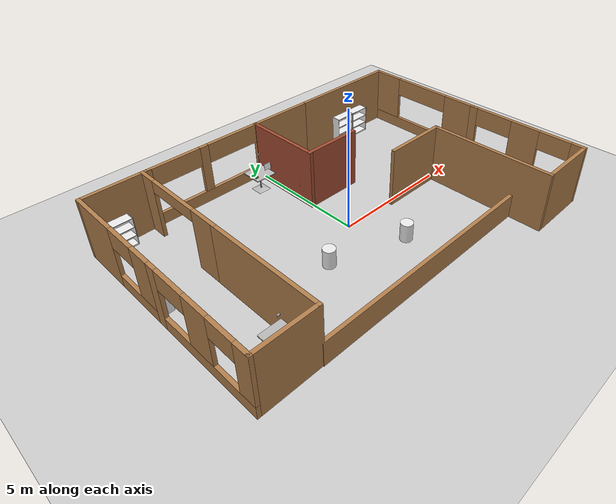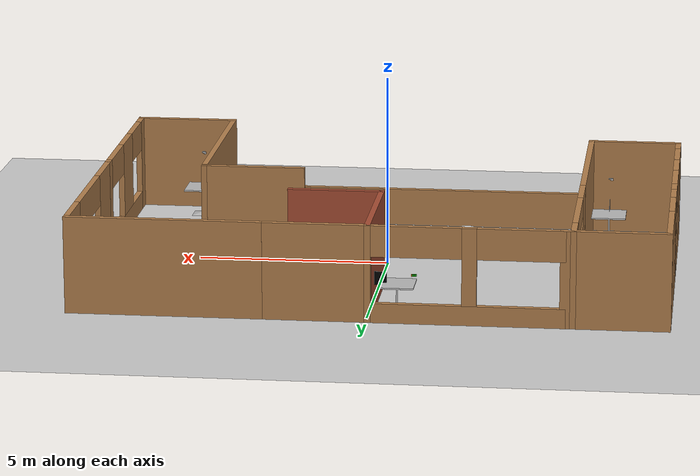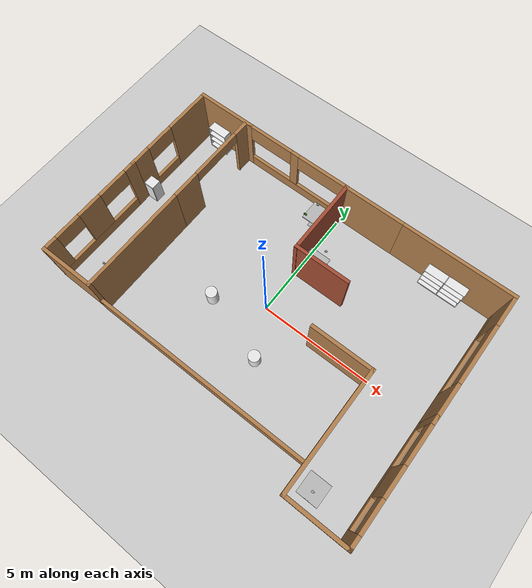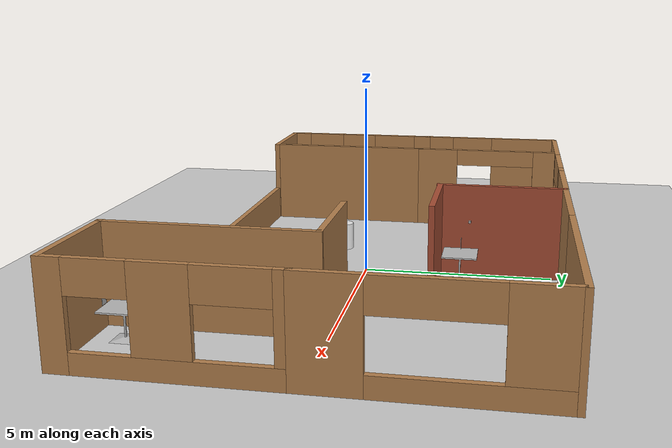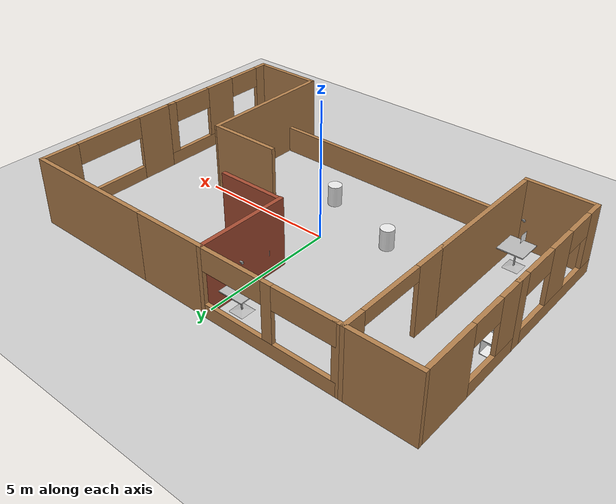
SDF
<sdf version='1.4'>
  <world name='default'>
    <!-- A global light source -->
    <include>
      <uri>model://sun</uri>
    </include>

    <!-- A ground plane -->
    <include>
      <uri>model://ground_plane</uri>
    </include>

    <physics type="ode">
      <real_time_update_rate>1000.0</real_time_update_rate>
      <max_step_size>0.001</max_step_size>
      <real_time_factor>1</real_time_factor>
      <ode>
        <solver>
          <type>quick</type>
          <iters>150</iters>
          <precon_iters>0</precon_iters>
          <sor>1.400000</sor>
          <use_dynamic_moi_rescaling>1</use_dynamic_moi_rescaling>
        </solver>
        <constraints>
          <cfm>0.00001</cfm>
          <erp>0.2</erp>
          <contact_max_correcting_vel>2000.000000</contact_max_correcting_vel>
          <contact_surface_layer>0.01000</contact_surface_layer>
        </constraints>
      </ode>
    </physics>

  <model name="marker_to_find">
    <include>
      <static>true</static>
      <uri>model://aruco_marker_0</uri>
    </include>
    <pose>-7.186030 1.111473 0.8183330 0 0 1.57</pose>
  </model>

  <model name="table_1_marker">
    <include>
      <static>true</static>
      <uri>model://aruco_marker_1</uri>
    </include>
    <pose>-5.700323 -3.155610 0.889384 0 0 1.57</pose>
  </model>

  <model name="table_2_marker">
    <include>
      <static>true</static>
      <uri>model://aruco_marker_2</uri>
    </include>
    <pose>-0.264755 4.42376 0.889384 0 0 3.14</pose>
  </model>

  <!-- Part on table 2 -->
  <model name="assembly_battery_green_0">
    <include>
      <static>false</static>
      <uri>model://assembly_battery_green_ariac</uri>
    </include>
    <pose>-1.093374 4.087609 0.889384 0 0 0</pose>
  </model>

  <model name="table_3_marker">
    <include>
      <static>true</static>
      <uri>model://aruco_marker_3</uri>
    </include>
    <pose>0.045670 2.6 0.889384 0 0 0</pose>
  </model>

  <model name="table_4_marker">
    <include>
      <static>true</static>
      <uri>model://aruco_marker_0</uri>
    </include>
    <pose>5.65 -4.903477 0.889384 0 0 1.57</pose>
  </model>

  <model name="logical_camera_1">
      <static>true</static>
      <pose>-5.739203 -2.837389 1.701710 3.141593 1.570792 0.0</pose>
      <plugin name="ros_logical_camera" filename="libROSLogicalCameraPlugin.so">
        <robotNamespace>logical_camera</robotNamespace>
        <position_noise>
          <noise>
            <type>gaussian</type>
            <mean>0.0</mean>
            <stddev>0.001</stddev>
          </noise>
        </position_noise>
        <orientation_noise>
          <noise>
            <type>gaussian</type>
            <mean>0.0</mean>
            <stddev>0.01</stddev>
          </noise>
        </orientation_noise>
        <known_model_types>
          <type>assembly_battery_red_ariac</type>
          <type>assembly_battery_green_ariac</type>
          <type>assembly_battery_blue_ariac</type>
          <type>assembly_pump_red_ariac</type>
          <type>assembly_pump_green_ariac</type>
          <type>assembly_pump_blue_ariac</type>
        </known_model_types>
        <anonymize_models>false</anonymize_models>
        <activation_topic>/ariac/sensor_enable</activation_topic>
      </plugin>
      <link name="link">
        <gravity>false</gravity>
        <inertial>
          <mass>0.1</mass>
          <inertia>
            <ixx>0.000166667</ixx>
            <iyy>0.000166667</iyy>
            <izz>0.000166667</izz>
          </inertia>
        </inertial>

        <visual name="visual">
          <pose>0 0.02 0 0 0 -1.5708</pose>
          <geometry>
            <mesh>
              <uri>model://logical_camera_ariac/meshes/camera.dae</uri>
            </mesh>
          </geometry>
        </visual>

        <sensor name="logical_camera" type="logical_camera">
          <logical_camera>
            <near>0.2</near>
            <far>1.1</far>
            <horizontal_fov>1.5</horizontal_fov>
            <aspect_ratio>1.2</aspect_ratio>
          </logical_camera>

          <visualize>True</visualize>
          <always_on>true</always_on>
          <update_rate>10</update_rate>
        </sensor>
      </link>
    </model>

  <model name="logical_camera_2">
      <static>true</static>
      <pose>-0.703821 4.357522 1.701710 3.141593 1.570792 0.0</pose>
      <plugin name="ros_logical_camera" filename="libROSLogicalCameraPlugin.so">
        <robotNamespace>logical_camera</robotNamespace>
        <position_noise>
          <noise>
            <type>gaussian</type>
            <mean>0.0</mean>
            <stddev>0.001</stddev>
          </noise>
        </position_noise>
        <orientation_noise>
          <noise>
            <type>gaussian</type>
            <mean>0.0</mean>
            <stddev>0.01</stddev>
          </noise>
        </orientation_noise>
        <known_model_types>
          <type>assembly_battery_red</type>
          <type>assembly_battery_green</type>
          <type>assembly_battery_blue</type>
          <type>assembly_pump_red</type>
          <type>assembly_pump_green</type>
          <type>assembly_pump_blue</type>
        </known_model_types>
        <anonymize_models>false</anonymize_models>
        <activation_topic>/ariac/sensor_enable</activation_topic>
      </plugin>
      <link name="link">
        <gravity>false</gravity>
        <inertial>
          <mass>0.1</mass>
          <inertia>
            <ixx>0.000166667</ixx>
            <iyy>0.000166667</iyy>
            <izz>0.000166667</izz>
          </inertia>
        </inertial>

        <visual name="visual">
          <pose>0 0.02 0 0 0 -1.5708</pose>
          <geometry>
            <mesh>
              <uri>model://logical_camera_ariac/meshes/camera.dae</uri>
            </mesh>
          </geometry>
        </visual>

        <sensor name="logical_camera" type="logical_camera">
          <logical_camera>
            <near>0.2</near>
            <far>1.1</far>
            <horizontal_fov>1.5</horizontal_fov>
            <aspect_ratio>1.2</aspect_ratio>
          </logical_camera>

          <visualize>True</visualize>
          <always_on>true</always_on>
          <update_rate>10</update_rate>
        </sensor>
      </link>
    </model>

    <model name="logical_camera_3">
      <static>true</static>
      <pose>0.786694 2.865128 1.701710 3.141593 1.570792 0.0</pose>
      <plugin name="ros_logical_camera" filename="libROSLogicalCameraPlugin.so">
        <robotNamespace>logical_camera</robotNamespace>
        <position_noise>
          <noise>
            <type>gaussian</type>
            <mean>0.0</mean>
            <stddev>0.001</stddev>
          </noise>
        </position_noise>
        <orientation_noise>
          <noise>
            <type>gaussian</type>
            <mean>0.0</mean>
            <stddev>0.01</stddev>
          </noise>
        </orientation_noise>
        <known_model_types>
          <type>assembly_battery_red_ariac</type>
          <type>assembly_battery_green_ariac</type>
          <type>assembly_battery_blue_ariac</type>
          <type>assembly_pump_red_ariac</type>
          <type>assembly_pump_green_ariac</type>
          <type>assembly_pump_blue_ariac</type>
        </known_model_types>
        <anonymize_models>false</anonymize_models>
        <activation_topic>/ariac/sensor_enable</activation_topic>
      </plugin>
      <link name="link">
        <gravity>false</gravity>
        <inertial>
          <mass>0.1</mass>
          <inertia>
            <ixx>0.000166667</ixx>
            <iyy>0.000166667</iyy>
            <izz>0.000166667</izz>
          </inertia>
        </inertial>

        <visual name="visual">
          <pose>0 0.02 0 0 0 -1.5708</pose>
          <geometry>
            <mesh>
              <uri>model://logical_camera_ariac/meshes/camera.dae</uri>
            </mesh>
          </geometry>
        </visual>

        <sensor name="logical_camera" type="logical_camera">
          <logical_camera>
            <near>0.2</near>
            <far>1.1</far>
            <horizontal_fov>1.5</horizontal_fov>
            <aspect_ratio>1.2</aspect_ratio>
          </logical_camera>

          <visualize>True</visualize>
          <always_on>true</always_on>
          <update_rate>10</update_rate>
        </sensor>
      </link>
    </model>

  <model name="logical_camera_4">
      <static>true</static>
      <pose>5.623647 -4.567452 1.701710 3.141593 1.570792 0.0</pose>
      <plugin name="ros_logical_camera" filename="libROSLogicalCameraPlugin.so">
        <robotNamespace>logical_camera</robotNamespace>
        <position_noise>
          <noise>
            <type>gaussian</type>
            <mean>0.0</mean>
            <stddev>0.001</stddev>
          </noise>
        </position_noise>
        <orientation_noise>
          <noise>
            <type>gaussian</type>
            <mean>0.0</mean>
            <stddev>0.01</stddev>
          </noise>
        </orientation_noise>
        <known_model_types>
          <type>assembly_battery_red_ariac</type>
          <type>assembly_battery_green_ariac</type>
          <type>assembly_battery_blue_ariac</type>
          <type>assembly_pump_red_ariac</type>
          <type>assembly_pump_green_ariac</type>
          <type>assembly_pump_blue_ariac</type>
        </known_model_types>
        <anonymize_models>false</anonymize_models>
        <activation_topic>/ariac/sensor_enable</activation_topic>
      </plugin>
      <link name="link">
        <gravity>false</gravity>
        <inertial>
          <mass>0.1</mass>
          <inertia>
            <ixx>0.000166667</ixx>
            <iyy>0.000166667</iyy>
            <izz>0.000166667</izz>
          </inertia>
        </inertial>

        <visual name="visual">
          <pose>0 0.02 0 0 0 -1.5708</pose>
          <geometry>
            <mesh>
              <uri>model://logical_camera_ariac/meshes/camera.dae</uri>
            </mesh>
          </geometry>
        </visual>

        <sensor name="logical_camera" type="logical_camera">
          <logical_camera>
            <near>0.2</near>
            <far>1.1</far>
            <horizontal_fov>1.5</horizontal_fov>
            <aspect_ratio>1.2</aspect_ratio>
          </logical_camera>

          <visualize>True</visualize>
          <always_on>true</always_on>
          <update_rate>10</update_rate>
        </sensor>
      </link>
    </model>

    <include>
      <uri>model://house</uri>
    </include>

    <scene>
      <ambient>0.4 0.4 0.4 1</ambient>
      <background>0.7 0.7 0.7 1</background>
      <shadows>true</shadows>
    </scene>

    <gui fullscreen='0'>
      <camera name='user_camera'>
        <pose frame=''>-2.59929 -10.2985 12.5136 0 0.861798 1.34159</pose>
        <view_controller>orbit</view_controller>
      </camera>
    </gui>
  </world>
</sdf>

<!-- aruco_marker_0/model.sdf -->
<sdf version='1.6'>
  <model name='aruco_marker_0'>
    <link name='link_0'>
      <pose frame=''>0 0 0 0 -0 0</pose>
      <inertial>
        <mass>1</mass>
        <inertia>
          <ixx>0</ixx>
          <ixy>0</ixy>
          <ixz>0</ixz>
          <iyy>0</iyy>
          <iyz>0</iyz>
          <izz>0</izz>
        </inertia>
      </inertial>
      <visual name='visual'>
        <pose frame=''>0 0 0 0 -0 0</pose>
        <geometry>
          <mesh>
            <uri>file://isr-testbed/aruco_marker_0/aruco_marker_0.dae</uri>
            <scale>0.1 0.1 0.1</scale>
          </mesh>
        </geometry>
        <material>
          <lighting>1</lighting>
          <script>
            <uri>file://media/materials/scripts/gazebo.material</uri>
            <name>Gazebo/DepthMapVS</name>
          </script>
          <ambient>0.3 0.3 0.3 1</ambient>
          <diffuse>0.7 0.7 0.7 1</diffuse>
          <specular>0.01 0.01 0.01 1</specular>
          <emissive>0 0 0 1</emissive>
        </material>
        <transparency>0</transparency>
        <cast_shadows>1</cast_shadows>
      </visual>
      <collision name='collision'>
        <laser_retro>0</laser_retro>
        <max_contacts>10</max_contacts>
        <pose frame=''>0 0 0 0 -0 0</pose>
        <geometry>
          <mesh>
            <uri>file://isr-testbed/aruco_marker_0/aruco_marker_0.dae</uri>
            <scale>0.1 0.1 0.1</scale>
          </mesh>
        </geometry>
        <surface>
          <friction>
            <ode>
              <mu>1</mu>
              <mu2>1</mu2>
              <fdir1>0 0 0</fdir1>
              <slip1>0</slip1>
              <slip2>0</slip2>
            </ode>
            <torsional>
              <coefficient>1</coefficient>
              <patch_radius>0</patch_radius>
              <surface_radius>0</surface_radius>
              <use_patch_radius>1</use_patch_radius>
              <ode>
                <slip>0</slip>
              </ode>
            </torsional>
          </friction>
          <bounce>
            <restitution_coefficient>0</restitution_coefficient>
            <threshold>1e+06</threshold>
          </bounce>
          <contact>
            <collide_without_contact>0</collide_without_contact>
            <collide_without_contact_bitmask>1</collide_without_contact_bitmask>
            <collide_bitmask>1</collide_bitmask>
            <ode>
              <soft_cfm>0</soft_cfm>
              <soft_erp>0.2</soft_erp>
              <kp>1e+13</kp>
              <kd>1</kd>
              <max_vel>0.01</max_vel>
              <min_depth>0</min_depth>
            </ode>
            <bullet>
              <split_impulse>1</split_impulse>
              <split_impulse_penetration_threshold>-0.01</split_impulse_penetration_threshold>
              <soft_cfm>0</soft_cfm>
              <soft_erp>0.2</soft_erp>
              <kp>1e+13</kp>
              <kd>1</kd>
            </bullet>
          </contact>
        </surface>
      </collision>
    </link>
    <static>1</static>
    <allow_auto_disable>1</allow_auto_disable>
  </model>
</sdf>

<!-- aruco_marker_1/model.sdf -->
<sdf version="1.9">
  <model name="aruco_marker_1">
    <static>true</static>

    <link name="link">
      <visual name="front">
        <pose>0 0 0 0 0 0</pose>
        <geometry>
          <box>
            <size>0.35 0.002 0.35</size>
          </box>
        </geometry>

        <material>
          <ambient>1 1 1 1</ambient>
          <diffuse>1 1 1 1</diffuse>
          <specular>0.1 0.1 0.1 1</specular>
          <emissive>0 0 0 1</emissive>

          <pbr>
            <metal>
              <albedo_map>
                model://aruco/aruco_marker_1/materials/textures/marker_1.png
              </albedo_map>
              <emissive_map>
                model://aruco/aruco_marker_1/materials/textures/marker_1.png
              </emissive_map>
            </metal>
          </pbr>
        </material>
      </visual>

      <visual name="back">
        <pose>0 -0.002 0 0 0 3.1416</pose>
        <geometry>
          <box>
            <size>0.35 0.002 0.35</size>
          </box>
        </geometry>
        <material>
          <ambient>0 0 0 1</ambient>
          <diffuse>0 0 0 1</diffuse>
        </material>
      </visual>

    </link>

  </model>
</sdf>

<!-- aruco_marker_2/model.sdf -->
<sdf version="1.9">
  <model name="aruco_marker_2">
    <static>true</static>

    <link name="link">
      <visual name="front">
        <pose>0 0 0 0 0 0</pose>
        <geometry>
          <box>
            <size>0.35 0.002 0.35</size>
          </box>
        </geometry>

        <material>
          <ambient>1 1 1 1</ambient>
          <diffuse>1 1 1 1</diffuse>
          <specular>0.1 0.1 0.1 1</specular>
          <emissive>0 0 0 1</emissive>

          <pbr>
            <metal>
              <albedo_map>
                model://aruco/aruco_marker_2/materials/textures/marker_2.png
              </albedo_map>
              <emissive_map>
                model://aruco/aruco_marker_2/materials/textures/marker_2.png
              </emissive_map>
            </metal>
          </pbr>
        </material>
      </visual>

      <visual name="back">
        <pose>0 -0.002 0 0 0 3.1416</pose>
        <geometry>
          <box>
            <size>0.35 0.002 0.35</size>
          </box>
        </geometry>
        <material>
          <ambient>0 0 0 1</ambient>
          <diffuse>0 0 0 1</diffuse>
        </material>
      </visual>

    </link>

  </model>
</sdf>

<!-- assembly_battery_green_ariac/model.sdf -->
<sdf version="1.6">
  <model name="assembly_battery_green_ariac">
    <link name="link">
      <inertial>
        <pose>0 0 0.0004 0 0 0</pose>
        <mass>0.5</mass>
        <inertia>
          <ixx>0.0009</ixx>
          <ixy>0</ixy>
          <ixz>0</ixz>
          <iyy>0.0009</iyy>
          <iyz>0</iyz>
          <izz>0.0009</izz>
        </inertia>
      </inertial>
      <collision name='collision'>
        <pose frame=''>0 0 0 0 0 0</pose>
        <geometry>
            <mesh>
            <uri>model://assembly_battery_blue_ariac/meshes/assembly_battery.stl</uri>
            <scale>0.98 1.0 1.0</scale>
            </mesh>
          </geometry>
        <surface>
          <contact>
            <ode>
              <max_vel>0.1</max_vel>
              <min_depth>0.001</min_depth>
            </ode>
          </contact>
        </surface>
      </collision>
      <visual name="visual">
         <geometry>
           <mesh>
             <uri>model://assembly_battery_green_ariac/meshes/battery_part_green.dae</uri>
            <scale>0.98 1.0 1.0</scale>
           </mesh>
         </geometry>
       </visual>
    </link>
  </model>
</sdf>

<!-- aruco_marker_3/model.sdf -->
<sdf version="1.9">
  <model name="aruco_marker_3">
    <static>true</static>

    <link name="link">
      <visual name="front">
        <pose>0 0 0 0 0 0</pose>
        <geometry>
          <box>
            <size>0.35 0.002 0.35</size>
          </box>
        </geometry>

        <material>
          <ambient>1 1 1 1</ambient>
          <diffuse>1 1 1 1</diffuse>
          <specular>0.1 0.1 0.1 1</specular>
          <emissive>0 0 0 1</emissive>

          <pbr>
            <metal>
              <albedo_map>
                model://aruco/aruco_marker_3/materials/textures/marker_3.png
              </albedo_map>
              <emissive_map>
                model://aruco/aruco_marker_3/materials/textures/marker_3.png
              </emissive_map>
            </metal>
          </pbr>
        </material>
      </visual>

      <visual name="back">
        <pose>0 -0.002 0 0 0 3.1416</pose>
        <geometry>
          <box>
            <size>0.35 0.002 0.35</size>
          </box>
        </geometry>
        <material>
          <ambient>0 0 0 1</ambient>
          <diffuse>0 0 0 1</diffuse>
        </material>
      </visual>

    </link>

  </model>
</sdf>

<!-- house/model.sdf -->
<sdf version='1.6'>
  <model name='house'>

<link name='post2'>
        <collision name='pole_2'>
          <pose>1 -2 0.25 0 0 0</pose>
          <geometry>
            <cylinder>
              <radius>0.25</radius>
              <length>1</length>
            </cylinder>
          </geometry>
          <max_contacts>10</max_contacts>
          <surface>
            <bounce/>
            <friction>
              <ode/>
            </friction>
            <contact>
              <ode/>
            </contact>
          </surface>
        </collision>

        <visual name='pole_2'>
          <pose>1 -2 0.25 0 0 0</pose>
          <geometry>
            <cylinder>
              <radius>0.25</radius>
              <length>1</length>
            </cylinder>
          </geometry>
          <material>
            <script>
              <uri>file://media/materials/scripts/gazebo.material</uri>
              <name>Gazebo/White</name>
            </script>
          </material>
        </visual>
    </link>

      <link name='post1'>
        <collision name='pole_1'>
          <pose>-2 -1 0.25 0 0 0</pose>
          <geometry>
            <cylinder>
              <radius>0.25</radius>
              <length>1</length>
            </cylinder>
          </geometry>
          <max_contacts>10</max_contacts>
          <surface>
            <bounce/>
            <friction>
              <ode/>
            </friction>
            <contact>
              <ode/>
            </contact>
          </surface>
        </collision>

        <visual name='pole_1'>
          <pose>-2 -1 0.25 0 0 0</pose>
          <geometry>
            <cylinder>
              <radius>0.25</radius>
              <length>1</length>
            </cylinder>
          </geometry>
          <material>
            <script>
              <uri>file://media/materials/scripts/gazebo.material</uri>
              <name>Gazebo/White</name>
            </script>
          </material>
        </visual>
    </link>
    <link name='Wall_101'>
      <pose frame=''>-0.05 3.6 0 0 0 -1.5708</pose>
      <self_collide>0</self_collide>
      <kinematic>0</kinematic>
      <visual name='Wall_101_Visual'>
        <pose frame=''>0 0 1.25 0 -0 0</pose>
        <geometry>
          <box>
            <size>3.4 0.15 2.5</size>
          </box>
        </geometry>
        <material>
          <script>
            <uri>file://media/materials/scripts/gazebo.material</uri>
            <name>Gazebo/Bricks</name>
          </script>
          <ambient>1 1 1 1</ambient>
          <diffuse>1 1 1 1</diffuse>
          <specular>0.2 0.2 0.2 1</specular>
          <emissive>0 0 0 1</emissive>
        </material>
        <cast_shadows>1</cast_shadows>
        <transparency>0</transparency>
      </visual>
      <collision name='Wall_101_Collision'>
        <laser_retro>0</laser_retro>
        <max_contacts>10</max_contacts>
        <pose frame=''>0 0 1.25 0 -0 0</pose>
        <geometry>
          <box>
            <size>3.4 0.15 2.5</size>
          </box>
        </geometry>
        <surface>
          <friction>
            <ode>
              <mu>1</mu>
              <mu2>1</mu2>
              <fdir1>0 0 0</fdir1>
              <slip1>0</slip1>
              <slip2>0</slip2>
            </ode>
            <torsional>
              <coefficient>1</coefficient>
              <patch_radius>0</patch_radius>
              <surface_radius>0</surface_radius>
              <use_patch_radius>1</use_patch_radius>
              <ode>
                <slip>0</slip>
              </ode>
            </torsional>
          </friction>
          <bounce>
            <restitution_coefficient>0</restitution_coefficient>
            <threshold>1e+06</threshold>
          </bounce>
          <contact>
            <collide_without_contact>0</collide_without_contact>
            <collide_without_contact_bitmask>1</collide_without_contact_bitmask>
            <collide_bitmask>1</collide_bitmask>
            <ode>
              <soft_cfm>0</soft_cfm>
              <soft_erp>0.2</soft_erp>
              <kp>1e+13</kp>
              <kd>1</kd>
              <max_vel>0.01</max_vel>
              <min_depth>0</min_depth>
            </ode>
            <bullet>
              <split_impulse>1</split_impulse>
              <split_impulse_penetration_threshold>-0.01</split_impulse_penetration_threshold>
              <soft_cfm>0</soft_cfm>
              <soft_erp>0.2</soft_erp>
              <kp>1e+13</kp>
              <kd>1</kd>
            </bullet>
          </contact>
        </surface>
      </collision>
    </link>
    <link name='Wall_108'>
      <pose frame=''>0.7 -3.95 0 0 -0 0</pose>
      <self_collide>0</self_collide>
      <kinematic>0</kinematic>
      <visual name='Wall_108_Visual_0'>
        <pose frame=''>-0.856324 0 0.5 0 -0 0</pose>
        <geometry>
          <box>
            <size>10 0.15 1</size>
          </box>
        </geometry>
        <material>
          <script>
            <uri>file://media/materials/scripts/gazebo.material</uri>
            <name>Gazebo/Wood</name>
          </script>
          <ambient>1 1 1 1</ambient>
          <diffuse>1 1 1 1</diffuse>
          <specular>0.2 0.2 0.2 1</specular>
          <emissive>0 0 0 1</emissive>
        </material>
        <cast_shadows>1</cast_shadows>
        <transparency>0</transparency>
      </visual>
      <collision name='Wall_108_Collision_0'>
        <laser_retro>0</laser_retro>
        <max_contacts>10</max_contacts>
        <pose frame=''>-0.856324 0 0.5 0 -0 0</pose>
        <geometry>
          <box>
            <size>10 0.15 1</size>
          </box>
        </geometry>
        <surface>
          <friction>
            <ode>
              <mu>1</mu>
              <mu2>1</mu2>
              <fdir1>0 0 0</fdir1>
              <slip1>0</slip1>
              <slip2>0</slip2>
            </ode>
            <torsional>
              <coefficient>1</coefficient>
              <patch_radius>0</patch_radius>
              <surface_radius>0</surface_radius>
              <use_patch_radius>1</use_patch_radius>
              <ode>
                <slip>0</slip>
              </ode>
            </torsional>
          </friction>
          <bounce>
            <restitution_coefficient>0</restitution_coefficient>
            <threshold>1e+06</threshold>
          </bounce>
          <contact>
            <collide_without_contact>0</collide_without_contact>
            <collide_without_contact_bitmask>1</collide_without_contact_bitmask>
            <collide_bitmask>1</collide_bitmask>
            <ode>
              <soft_cfm>0</soft_cfm>
              <soft_erp>0.2</soft_erp>
              <kp>1e+13</kp>
              <kd>1</kd>
              <max_vel>0.01</max_vel>
              <min_depth>0</min_depth>
            </ode>
            <bullet>
              <split_impulse>1</split_impulse>
              <split_impulse_penetration_threshold>-0.01</split_impulse_penetration_threshold>
              <soft_cfm>0</soft_cfm>
              <soft_erp>0.2</soft_erp>
              <kp>1e+13</kp>
              <kd>1</kd>
            </bullet>
          </contact>
        </surface>
      </collision>
    </link>
    <link name='Wall_81'>
      <pose frame=''>5.07752 5.2688 0 0 -0 3.14159</pose>
      <self_collide>0</self_collide>
      <kinematic>0</kinematic>
      <visual name='Wall_81_Visual'>
        <pose frame=''>0 0 1.25 0 -0 0</pose>
        <geometry>
          <box>
            <size>5 0.15 2.5</size>
          </box>
        </geometry>
        <material>
          <script>
            <uri>file://media/materials/scripts/gazebo.material</uri>
            <name>Gazebo/Wood</name>
          </script>
          <ambient>1 1 1 1</ambient>
          <diffuse>1 1 1 1</diffuse>
          <specular>0.2 0.2 0.2 1</specular>
          <emissive>0 0 0 1</emissive>
        </material>
        <cast_shadows>1</cast_shadows>
        <transparency>0</transparency>
      </visual>
      <collision name='Wall_81_Collision'>
        <laser_retro>0</laser_retro>
        <max_contacts>10</max_contacts>
        <pose frame=''>0 0 1.25 0 -0 0</pose>
        <geometry>
          <box>
            <size>5 0.15 2.5</size>
          </box>
        </geometry>
        <surface>
          <friction>
            <ode>
              <mu>1</mu>
              <mu2>1</mu2>
              <fdir1>0 0 0</fdir1>
              <slip1>0</slip1>
              <slip2>0</slip2>
            </ode>
            <torsional>
              <coefficient>1</coefficient>
              <patch_radius>0</patch_radius>
              <surface_radius>0</surface_radius>
              <use_patch_radius>1</use_patch_radius>
              <ode>
                <slip>0</slip>
              </ode>
            </torsional>
          </friction>
          <bounce>
            <restitution_coefficient>0</restitution_coefficient>
            <threshold>1e+06</threshold>
          </bounce>
          <contact>
            <collide_without_contact>0</collide_without_contact>
            <collide_without_contact_bitmask>1</collide_without_contact_bitmask>
            <collide_bitmask>1</collide_bitmask>
            <ode>
              <soft_cfm>0</soft_cfm>
              <soft_erp>0.2</soft_erp>
              <kp>1e+13</kp>
              <kd>1</kd>
              <max_vel>0.01</max_vel>
              <min_depth>0</min_depth>
            </ode>
            <bullet>
              <split_impulse>1</split_impulse>
              <split_impulse_penetration_threshold>-0.01</split_impulse_penetration_threshold>
              <soft_cfm>0</soft_cfm>
              <soft_erp>0.2</soft_erp>
              <kp>1e+13</kp>
              <kd>1</kd>
            </bullet>
          </contact>
        </surface>
      </collision>
    </link>
    <link name='Wall_82'>
      <pose frame=''>1.25 5.26876 0 0 -0 3.14159</pose>
      <self_collide>0</self_collide>
      <kinematic>0</kinematic>
      <visual name='Wall_82_Visual'>
        <pose frame=''>0 0 1.25 0 -0 0</pose>
        <geometry>
          <box>
            <size>2.75 0.15 2.5</size>
          </box>
        </geometry>
        <material>
          <script>
            <uri>file://media/materials/scripts/gazebo.material</uri>
            <name>Gazebo/Wood</name>
          </script>
          <ambient>1 1 1 1</ambient>
          <diffuse>1 1 1 1</diffuse>
          <specular>0.2 0.2 0.2 1</specular>
          <emissive>0 0 0 1</emissive>
        </material>
        <cast_shadows>1</cast_shadows>
        <transparency>0</transparency>
      </visual>
      <collision name='Wall_82_Collision'>
        <laser_retro>0</laser_retro>
        <max_contacts>10</max_contacts>
        <pose frame=''>0 0 1.25 0 -0 0</pose>
        <geometry>
          <box>
            <size>2.75 0.15 2.5</size>
          </box>
        </geometry>
        <surface>
          <friction>
            <ode>
              <mu>1</mu>
              <mu2>1</mu2>
              <fdir1>0 0 0</fdir1>
              <slip1>0</slip1>
              <slip2>0</slip2>
            </ode>
            <torsional>
              <coefficient>1</coefficient>
              <patch_radius>0</patch_radius>
              <surface_radius>0</surface_radius>
              <use_patch_radius>1</use_patch_radius>
              <ode>
                <slip>0</slip>
              </ode>
            </torsional>
          </friction>
          <bounce>
            <restitution_coefficient>0</restitution_coefficient>
            <threshold>1e+06</threshold>
          </bounce>
          <contact>
            <collide_without_contact>0</collide_without_contact>
            <collide_without_contact_bitmask>1</collide_without_contact_bitmask>
            <collide_bitmask>1</collide_bitmask>
            <ode>
              <soft_cfm>0</soft_cfm>
              <soft_erp>0.2</soft_erp>
              <kp>1e+13</kp>
              <kd>1</kd>
              <max_vel>0.01</max_vel>
              <min_depth>0</min_depth>
            </ode>
            <bullet>
              <split_impulse>1</split_impulse>
              <split_impulse_penetration_threshold>-0.01</split_impulse_penetration_threshold>
              <soft_cfm>0</soft_cfm>
              <soft_erp>0.2</soft_erp>
              <kp>1e+13</kp>
              <kd>1</kd>
            </bullet>
          </contact>
        </surface>
      </collision>
    </link>
    <link name='Wall_83'>
      <pose frame=''>-2.475 5.275 0 0 -0 3.14159</pose>
      <self_collide>0</self_collide>
      <kinematic>0</kinematic>
      <visual name='Wall_83_Visual_2'>
        <pose frame=''>0.110246 0 1.5 0 -0 0</pose>
        <geometry>
          <box>
            <size>0.37052 0.15 2</size>
          </box>
        </geometry>
        <material>
          <script>
            <uri>file://media/materials/scripts/gazebo.material</uri>
            <name>Gazebo/Wood</name>
          </script>
          <ambient>1 1 1 1</ambient>
          <diffuse>1 1 1 1</diffuse>
          <specular>0.2 0.2 0.2 1</specular>
          <emissive>0 0 0 1</emissive>
        </material>
        <cast_shadows>1</cast_shadows>
        <transparency>0</transparency>
      </visual>
      <visual name='Wall_83_Visual_6'>
        <pose frame=''>1.39775 0 2.1 0 -0 0</pose>
        <geometry>
          <box>
            <size>2.20449 0.15 0.8</size>
          </box>
        </geometry>
        <material>
          <script>
            <uri>file://media/materials/scripts/gazebo.material</uri>
            <name>Gazebo/Wood</name>
          </script>
          <ambient>1 1 1 1</ambient>
          <diffuse>1 1 1 1</diffuse>
          <specular>0.2 0.2 0.2 1</specular>
          <emissive>0 0 0 1</emissive>
        </material>
        <cast_shadows>1</cast_shadows>
        <transparency>0</transparency>
      </visual>
      <visual name='Wall_83_Visual_3'>
        <pose frame=''>0.110246 0 1.5 0 -0 0</pose>
        <geometry>
          <box>
            <size>0.37052 0.15 2</size>
          </box>
        </geometry>
        <material>
          <script>
            <uri>file://media/materials/scripts/gazebo.material</uri>
            <name>Gazebo/Wood</name>
          </script>
          <ambient>1 1 1 1</ambient>
          <diffuse>1 1 1 1</diffuse>
          <specular>0.2 0.2 0.2 1</specular>
          <emissive>0 0 0 1</emissive>
        </material>
        <cast_shadows>1</cast_shadows>
        <transparency>0</transparency>
      </visual>
      <visual name='Wall_83_Visual_1'>
        <pose frame=''>0.080993 0 0.25 0 -0 0</pose>
        <geometry>
          <box>
            <size>4.83801 0.15 0.5</size>
          </box>
        </geometry>
        <material>
          <script>
            <uri>file://media/materials/scripts/gazebo.material</uri>
            <name>Gazebo/Wood</name>
          </script>
          <ambient>1 1 1 1</ambient>
          <diffuse>1 1 1 1</diffuse>
          <specular>0.2 0.2 0.2 1</specular>
          <emissive>0 0 0 1</emissive>
        </material>
        <cast_shadows>1</cast_shadows>
        <transparency>0</transparency>
      </visual>
      <visual name='Wall_83_Visual_4'>
        <pose frame=''>-1.20651 0 2.1 0 -0 0</pose>
        <geometry>
          <box>
            <size>2.263 0.15 0.8</size>
          </box>
        </geometry>
        <material>
          <script>
            <uri>file://media/materials/scripts/gazebo.material</uri>
            <name>Gazebo/Wood</name>
          </script>
          <ambient>1 1 1 1</ambient>
          <diffuse>1 1 1 1</diffuse>
          <specular>0.2 0.2 0.2 1</specular>
          <emissive>0 0 0 1</emissive>
        </material>
        <cast_shadows>1</cast_shadows>
        <transparency>0</transparency>
      </visual>
      <visual name='Wall_83_Visual_5'>
        <pose frame=''>1.39775 0 2.1 0 -0 0</pose>
        <geometry>
          <box>
            <size>2.20449 0.15 0.8</size>
          </box>
        </geometry>
        <material>
          <script>
            <uri>file://media/materials/scripts/gazebo.material</uri>
            <name>Gazebo/Wood</name>
          </script>
          <ambient>1 1 1 1</ambient>
          <diffuse>1 1 1 1</diffuse>
          <specular>0.2 0.2 0.2 1</specular>
          <emissive>0 0 0 1</emissive>
        </material>
        <cast_shadows>1</cast_shadows>
        <transparency>0</transparency>
      </visual>
      <visual name='Wall_83_Visual_0'>
        <pose frame=''>-2.41901 0 1.25 0 -0 0</pose>
        <geometry>
          <box>
            <size>0.161986 0.15 2.5</size>
          </box>
        </geometry>
        <material>
          <script>
            <uri>file://media/materials/scripts/gazebo.material</uri>
            <name>Gazebo/Wood</name>
          </script>
          <ambient>1 1 1 1</ambient>
          <diffuse>1 1 1 1</diffuse>
          <specular>0.2 0.2 0.2 1</specular>
          <emissive>0 0 0 1</emissive>
        </material>
        <cast_shadows>1</cast_shadows>
        <transparency>0</transparency>
      </visual>
      <collision name='Wall_83_Collision_4'>
        <laser_retro>0</laser_retro>
        <max_contacts>10</max_contacts>
        <pose frame=''>-1.20651 0 2.1 0 -0 0</pose>
        <geometry>
          <box>
            <size>2.263 0.15 0.8</size>
          </box>
        </geometry>
        <surface>
          <friction>
            <ode>
              <mu>1</mu>
              <mu2>1</mu2>
              <fdir1>0 0 0</fdir1>
              <slip1>0</slip1>
              <slip2>0</slip2>
            </ode>
            <torsional>
              <coefficient>1</coefficient>
              <patch_radius>0</patch_radius>
              <surface_radius>0</surface_radius>
              <use_patch_radius>1</use_patch_radius>
              <ode>
                <slip>0</slip>
              </ode>
            </torsional>
          </friction>
          <bounce>
            <restitution_coefficient>0</restitution_coefficient>
            <threshold>1e+06</threshold>
          </bounce>
          <contact>
            <collide_without_contact>0</collide_without_contact>
            <collide_without_contact_bitmask>1</collide_without_contact_bitmask>
            <collide_bitmask>1</collide_bitmask>
            <ode>
              <soft_cfm>0</soft_cfm>
              <soft_erp>0.2</soft_erp>
              <kp>1e+13</kp>
              <kd>1</kd>
              <max_vel>0.01</max_vel>
              <min_depth>0</min_depth>
            </ode>
            <bullet>
              <split_impulse>1</split_impulse>
              <split_impulse_penetration_threshold>-0.01</split_impulse_penetration_threshold>
              <soft_cfm>0</soft_cfm>
              <soft_erp>0.2</soft_erp>
              <kp>1e+13</kp>
              <kd>1</kd>
            </bullet>
          </contact>
        </surface>
      </collision>
      <collision name='Wall_83_Collision_2'>
        <laser_retro>0</laser_retro>
        <max_contacts>10</max_contacts>
        <pose frame=''>0.110246 0 1.5 0 -0 0</pose>
        <geometry>
          <box>
            <size>0.37052 0.15 2</size>
          </box>
        </geometry>
        <surface>
          <friction>
            <ode>
              <mu>1</mu>
              <mu2>1</mu2>
              <fdir1>0 0 0</fdir1>
              <slip1>0</slip1>
              <slip2>0</slip2>
            </ode>
            <torsional>
              <coefficient>1</coefficient>
              <patch_radius>0</patch_radius>
              <surface_radius>0</surface_radius>
              <use_patch_radius>1</use_patch_radius>
              <ode>
                <slip>0</slip>
              </ode>
            </torsional>
          </friction>
          <bounce>
            <restitution_coefficient>0</restitution_coefficient>
            <threshold>1e+06</threshold>
          </bounce>
          <contact>
            <collide_without_contact>0</collide_without_contact>
            <collide_without_contact_bitmask>1</collide_without_contact_bitmask>
            <collide_bitmask>1</collide_bitmask>
            <ode>
              <soft_cfm>0</soft_cfm>
              <soft_erp>0.2</soft_erp>
              <kp>1e+13</kp>
              <kd>1</kd>
              <max_vel>0.01</max_vel>
              <min_depth>0</min_depth>
            </ode>
            <bullet>
              <split_impulse>1</split_impulse>
              <split_impulse_penetration_threshold>-0.01</split_impulse_penetration_threshold>
              <soft_cfm>0</soft_cfm>
              <soft_erp>0.2</soft_erp>
              <kp>1e+13</kp>
              <kd>1</kd>
            </bullet>
          </contact>
        </surface>
      </collision>
      <collision name='Wall_83_Collision_6'>
        <laser_retro>0</laser_retro>
        <max_contacts>10</max_contacts>
        <pose frame=''>1.39775 0 2.1 0 -0 0</pose>
        <geometry>
          <box>
            <size>2.20449 0.15 0.8</size>
          </box>
        </geometry>
        <surface>
          <friction>
            <ode>
              <mu>1</mu>
              <mu2>1</mu2>
              <fdir1>0 0 0</fdir1>
              <slip1>0</slip1>
              <slip2>0</slip2>
            </ode>
            <torsional>
              <coefficient>1</coefficient>
              <patch_radius>0</patch_radius>
              <surface_radius>0</surface_radius>
              <use_patch_radius>1</use_patch_radius>
              <ode>
                <slip>0</slip>
              </ode>
            </torsional>
          </friction>
          <bounce>
            <restitution_coefficient>0</restitution_coefficient>
            <threshold>1e+06</threshold>
          </bounce>
          <contact>
            <collide_without_contact>0</collide_without_contact>
            <collide_without_contact_bitmask>1</collide_without_contact_bitmask>
            <collide_bitmask>1</collide_bitmask>
            <ode>
              <soft_cfm>0</soft_cfm>
              <soft_erp>0.2</soft_erp>
              <kp>1e+13</kp>
              <kd>1</kd>
              <max_vel>0.01</max_vel>
              <min_depth>0</min_depth>
            </ode>
            <bullet>
              <split_impulse>1</split_impulse>
              <split_impulse_penetration_threshold>-0.01</split_impulse_penetration_threshold>
              <soft_cfm>0</soft_cfm>
              <soft_erp>0.2</soft_erp>
              <kp>1e+13</kp>
              <kd>1</kd>
            </bullet>
          </contact>
        </surface>
      </collision>
      <collision name='Wall_83_Collision_0'>
        <laser_retro>0</laser_retro>
        <max_contacts>10</max_contacts>
        <pose frame=''>-2.41901 0 1.25 0 -0 0</pose>
        <geometry>
          <box>
            <size>0.161986 0.15 2.5</size>
          </box>
        </geometry>
        <surface>
          <friction>
            <ode>
              <mu>1</mu>
              <mu2>1</mu2>
              <fdir1>0 0 0</fdir1>
              <slip1>0</slip1>
              <slip2>0</slip2>
            </ode>
            <torsional>
              <coefficient>1</coefficient>
              <patch_radius>0</patch_radius>
              <surface_radius>0</surface_radius>
              <use_patch_radius>1</use_patch_radius>
              <ode>
                <slip>0</slip>
              </ode>
            </torsional>
          </friction>
          <bounce>
            <restitution_coefficient>0</restitution_coefficient>
            <threshold>1e+06</threshold>
          </bounce>
          <contact>
            <collide_without_contact>0</collide_without_contact>
            <collide_without_contact_bitmask>1</collide_without_contact_bitmask>
            <collide_bitmask>1</collide_bitmask>
            <ode>
              <soft_cfm>0</soft_cfm>
              <soft_erp>0.2</soft_erp>
              <kp>1e+13</kp>
              <kd>1</kd>
              <max_vel>0.01</max_vel>
              <min_depth>0</min_depth>
            </ode>
            <bullet>
              <split_impulse>1</split_impulse>
              <split_impulse_penetration_threshold>-0.01</split_impulse_penetration_threshold>
              <soft_cfm>0</soft_cfm>
              <soft_erp>0.2</soft_erp>
              <kp>1e+13</kp>
              <kd>1</kd>
            </bullet>
          </contact>
        </surface>
      </collision>
      <collision name='Wall_83_Collision_1'>
        <laser_retro>0</laser_retro>
        <max_contacts>10</max_contacts>
        <pose frame=''>0.080993 0 0.25 0 -0 0</pose>
        <geometry>
          <box>
            <size>4.83801 0.15 0.5</size>
          </box>
        </geometry>
        <surface>
          <friction>
            <ode>
              <mu>1</mu>
              <mu2>1</mu2>
              <fdir1>0 0 0</fdir1>
              <slip1>0</slip1>
              <slip2>0</slip2>
            </ode>
            <torsional>
              <coefficient>1</coefficient>
              <patch_radius>0</patch_radius>
              <surface_radius>0</surface_radius>
              <use_patch_radius>1</use_patch_radius>
              <ode>
                <slip>0</slip>
              </ode>
            </torsional>
          </friction>
          <bounce>
            <restitution_coefficient>0</restitution_coefficient>
            <threshold>1e+06</threshold>
          </bounce>
          <contact>
            <collide_without_contact>0</collide_without_contact>
            <collide_without_contact_bitmask>1</collide_without_contact_bitmask>
            <collide_bitmask>1</collide_bitmask>
            <ode>
              <soft_cfm>0</soft_cfm>
              <soft_erp>0.2</soft_erp>
              <kp>1e+13</kp>
              <kd>1</kd>
              <max_vel>0.01</max_vel>
              <min_depth>0</min_depth>
            </ode>
            <bullet>
              <split_impulse>1</split_impulse>
              <split_impulse_penetration_threshold>-0.01</split_impulse_penetration_threshold>
              <soft_cfm>0</soft_cfm>
              <soft_erp>0.2</soft_erp>
              <kp>1e+13</kp>
              <kd>1</kd>
            </bullet>
          </contact>
        </surface>
      </collision>
      <collision name='Wall_83_Collision_3'>
        <laser_retro>0</laser_retro>
        <max_contacts>10</max_contacts>
        <pose frame=''>0.110246 0 1.5 0 -0 0</pose>
        <geometry>
          <box>
            <size>0.37052 0.15 2</size>
          </box>
        </geometry>
        <surface>
          <friction>
            <ode>
              <mu>1</mu>
              <mu2>1</mu2>
              <fdir1>0 0 0</fdir1>
              <slip1>0</slip1>
              <slip2>0</slip2>
            </ode>
            <torsional>
              <coefficient>1</coefficient>
              <patch_radius>0</patch_radius>
              <surface_radius>0</surface_radius>
              <use_patch_radius>1</use_patch_radius>
              <ode>
                <slip>0</slip>
              </ode>
            </torsional>
          </friction>
          <bounce>
            <restitution_coefficient>0</restitution_coefficient>
            <threshold>1e+06</threshold>
          </bounce>
          <contact>
            <collide_without_contact>0</collide_without_contact>
            <collide_without_contact_bitmask>1</collide_without_contact_bitmask>
            <collide_bitmask>1</collide_bitmask>
            <ode>
              <soft_cfm>0</soft_cfm>
              <soft_erp>0.2</soft_erp>
              <kp>1e+13</kp>
              <kd>1</kd>
              <max_vel>0.01</max_vel>
              <min_depth>0</min_depth>
            </ode>
            <bullet>
              <split_impulse>1</split_impulse>
              <split_impulse_penetration_threshold>-0.01</split_impulse_penetration_threshold>
              <soft_cfm>0</soft_cfm>
              <soft_erp>0.2</soft_erp>
              <kp>1e+13</kp>
              <kd>1</kd>
            </bullet>
          </contact>
        </surface>
      </collision>
      <collision name='Wall_83_Collision_5'>
        <laser_retro>0</laser_retro>
        <max_contacts>10</max_contacts>
        <pose frame=''>1.39775 0 2.1 0 -0 0</pose>
        <geometry>
          <box>
            <size>2.20449 0.15 0.8</size>
          </box>
        </geometry>
        <surface>
          <friction>
            <ode>
              <mu>1</mu>
              <mu2>1</mu2>
              <fdir1>0 0 0</fdir1>
              <slip1>0</slip1>
              <slip2>0</slip2>
            </ode>
            <torsional>
              <coefficient>1</coefficient>
              <patch_radius>0</patch_radius>
              <surface_radius>0</surface_radius>
              <use_patch_radius>1</use_patch_radius>
              <ode>
                <slip>0</slip>
              </ode>
            </torsional>
          </friction>
          <bounce>
            <restitution_coefficient>0</restitution_coefficient>
            <threshold>1e+06</threshold>
          </bounce>
          <contact>
            <collide_without_contact>0</collide_without_contact>
            <collide_without_contact_bitmask>1</collide_without_contact_bitmask>
            <collide_bitmask>1</collide_bitmask>
            <ode>
              <soft_cfm>0</soft_cfm>
              <soft_erp>0.2</soft_erp>
              <kp>1e+13</kp>
              <kd>1</kd>
              <max_vel>0.01</max_vel>
              <min_depth>0</min_depth>
            </ode>
            <bullet>
              <split_impulse>1</split_impulse>
              <split_impulse_penetration_threshold>-0.01</split_impulse_penetration_threshold>
              <soft_cfm>0</soft_cfm>
              <soft_erp>0.2</soft_erp>
              <kp>1e+13</kp>
              <kd>1</kd>
            </bullet>
          </contact>
        </surface>
      </collision>
    </link>
    <link name='Wall_84'>
      <pose frame=''>-6.2 5.275 0 0 -0 3.14159</pose>
      <self_collide>0</self_collide>
      <kinematic>0</kinematic>
      <visual name='Wall_84_Visual'>
        <pose frame=''>0 0 1.25 0 -0 0</pose>
        <geometry>
          <box>
            <size>2.75 0.15 2.5</size>
          </box>
        </geometry>
        <material>
          <script>
            <uri>file://media/materials/scripts/gazebo.material</uri>
            <name>Gazebo/Wood</name>
          </script>
          <ambient>1 1 1 1</ambient>
          <diffuse>1 1 1 1</diffuse>
          <specular>0.2 0.2 0.2 1</specular>
          <emissive>0 0 0 1</emissive>
        </material>
        <cast_shadows>1</cast_shadows>
        <transparency>0</transparency>
      </visual>
      <collision name='Wall_84_Collision'>
        <laser_retro>0</laser_retro>
        <max_contacts>10</max_contacts>
        <pose frame=''>0 0 1.25 0 -0 0</pose>
        <geometry>
          <box>
            <size>2.75 0.15 2.5</size>
          </box>
        </geometry>
        <surface>
          <friction>
            <ode>
              <mu>1</mu>
              <mu2>1</mu2>
              <fdir1>0 0 0</fdir1>
              <slip1>0</slip1>
              <slip2>0</slip2>
            </ode>
            <torsional>
              <coefficient>1</coefficient>
              <patch_radius>0</patch_radius>
              <surface_radius>0</surface_radius>
              <use_patch_radius>1</use_patch_radius>
              <ode>
                <slip>0</slip>
              </ode>
            </torsional>
          </friction>
          <bounce>
            <restitution_coefficient>0</restitution_coefficient>
            <threshold>1e+06</threshold>
          </bounce>
          <contact>
            <collide_without_contact>0</collide_without_contact>
            <collide_without_contact_bitmask>1</collide_without_contact_bitmask>
            <collide_bitmask>1</collide_bitmask>
            <ode>
              <soft_cfm>0</soft_cfm>
              <soft_erp>0.2</soft_erp>
              <kp>1e+13</kp>
              <kd>1</kd>
              <max_vel>0.01</max_vel>
              <min_depth>0</min_depth>
            </ode>
            <bullet>
              <split_impulse>1</split_impulse>
              <split_impulse_penetration_threshold>-0.01</split_impulse_penetration_threshold>
              <soft_cfm>0</soft_cfm>
              <soft_erp>0.2</soft_erp>
              <kp>1e+13</kp>
              <kd>1</kd>
            </bullet>
          </contact>
        </surface>
      </collision>
    </link>
    <link name='Wall_85'>
      <pose frame=''>-7.5 3.1 0 0 0 -1.5708</pose>
      <self_collide>0</self_collide>
      <kinematic>0</kinematic>
      <visual name='Wall_85_Visual_3'>
        <pose frame=''>0.62212 0 2.1 0 -0 0</pose>
        <geometry>
          <box>
            <size>1.332 0.15 0.8</size>
          </box>
        </geometry>
        <material>
          <script>
            <uri>file://media/materials/scripts/gazebo.material</uri>
            <name>Gazebo/Wood</name>
          </script>
          <ambient>1 1 1 1</ambient>
          <diffuse>1 1 1 1</diffuse>
          <specular>0.2 0.2 0.2 1</specular>
          <emissive>0 0 0 1</emissive>
        </material>
        <cast_shadows>1</cast_shadows>
        <transparency>0</transparency>
      </visual>
      <visual name='Wall_85_Visual_2'>
        <pose frame=''>1.76906 0 1.5 0 -0 0</pose>
        <geometry>
          <box>
            <size>0.96188 0.15 2</size>
          </box>
        </geometry>
        <material>
          <script>
            <uri>file://media/materials/scripts/gazebo.material</uri>
            <name>Gazebo/Wood</name>
          </script>
          <ambient>1 1 1 1</ambient>
          <diffuse>1 1 1 1</diffuse>
          <specular>0.2 0.2 0.2 1</specular>
          <emissive>0 0 0 1</emissive>
        </material>
        <cast_shadows>1</cast_shadows>
        <transparency>0</transparency>
      </visual>
      <visual name='Wall_85_Visual_0'>
        <pose frame=''>-1.14694 0 1.25 0 -0 0</pose>
        <geometry>
          <box>
            <size>2.20612 0.15 2.5</size>
          </box>
        </geometry>
        <material>
          <script>
            <uri>file://media/materials/scripts/gazebo.material</uri>
            <name>Gazebo/Wood</name>
          </script>
          <ambient>1 1 1 1</ambient>
          <diffuse>1 1 1 1</diffuse>
          <specular>0.2 0.2 0.2 1</specular>
          <emissive>0 0 0 1</emissive>
        </material>
        <cast_shadows>1</cast_shadows>
        <transparency>0</transparency>
      </visual>
      <visual name='Wall_85_Visual_1'>
        <pose frame=''>1.10306 0 0.25 0 -0 0</pose>
        <geometry>
          <box>
            <size>2.29388 0.15 0.5</size>
          </box>
        </geometry>
        <material>
          <script>
            <uri>file://media/materials/scripts/gazebo.material</uri>
            <name>Gazebo/Wood</name>
          </script>
          <ambient>1 1 1 1</ambient>
          <diffuse>1 1 1 1</diffuse>
          <specular>0.2 0.2 0.2 1</specular>
          <emissive>0 0 0 1</emissive>
        </material>
        <cast_shadows>1</cast_shadows>
        <transparency>0</transparency>
      </visual>
      <collision name='Wall_85_Collision_3'>
        <laser_retro>0</laser_retro>
        <max_contacts>10</max_contacts>
        <pose frame=''>0.62212 0 2.1 0 -0 0</pose>
        <geometry>
          <box>
            <size>1.332 0.15 0.8</size>
          </box>
        </geometry>
        <surface>
          <friction>
            <ode>
              <mu>1</mu>
              <mu2>1</mu2>
              <fdir1>0 0 0</fdir1>
              <slip1>0</slip1>
              <slip2>0</slip2>
            </ode>
            <torsional>
              <coefficient>1</coefficient>
              <patch_radius>0</patch_radius>
              <surface_radius>0</surface_radius>
              <use_patch_radius>1</use_patch_radius>
              <ode>
                <slip>0</slip>
              </ode>
            </torsional>
          </friction>
          <bounce>
            <restitution_coefficient>0</restitution_coefficient>
            <threshold>1e+06</threshold>
          </bounce>
          <contact>
            <collide_without_contact>0</collide_without_contact>
            <collide_without_contact_bitmask>1</collide_without_contact_bitmask>
            <collide_bitmask>1</collide_bitmask>
            <ode>
              <soft_cfm>0</soft_cfm>
              <soft_erp>0.2</soft_erp>
              <kp>1e+13</kp>
              <kd>1</kd>
              <max_vel>0.01</max_vel>
              <min_depth>0</min_depth>
            </ode>
            <bullet>
              <split_impulse>1</split_impulse>
              <split_impulse_penetration_threshold>-0.01</split_impulse_penetration_threshold>
              <soft_cfm>0</soft_cfm>
              <soft_erp>0.2</soft_erp>
              <kp>1e+13</kp>
              <kd>1</kd>
            </bullet>
          </contact>
        </surface>
      </collision>
      <collision name='Wall_85_Collision_2'>
        <laser_retro>0</laser_retro>
        <max_contacts>10</max_contacts>
        <pose frame=''>1.76906 0 1.5 0 -0 0</pose>
        <geometry>
          <box>
            <size>0.96188 0.15 2</size>
          </box>
        </geometry>
        <surface>
          <friction>
            <ode>
              <mu>1</mu>
              <mu2>1</mu2>
              <fdir1>0 0 0</fdir1>
              <slip1>0</slip1>
              <slip2>0</slip2>
            </ode>
            <torsional>
              <coefficient>1</coefficient>
              <patch_radius>0</patch_radius>
              <surface_radius>0</surface_radius>
              <use_patch_radius>1</use_patch_radius>
              <ode>
                <slip>0</slip>
              </ode>
            </torsional>
          </friction>
          <bounce>
            <restitution_coefficient>0</restitution_coefficient>
            <threshold>1e+06</threshold>
          </bounce>
          <contact>
            <collide_without_contact>0</collide_without_contact>
            <collide_without_contact_bitmask>1</collide_without_contact_bitmask>
            <collide_bitmask>1</collide_bitmask>
            <ode>
              <soft_cfm>0</soft_cfm>
              <soft_erp>0.2</soft_erp>
              <kp>1e+13</kp>
              <kd>1</kd>
              <max_vel>0.01</max_vel>
              <min_depth>0</min_depth>
            </ode>
            <bullet>
              <split_impulse>1</split_impulse>
              <split_impulse_penetration_threshold>-0.01</split_impulse_penetration_threshold>
              <soft_cfm>0</soft_cfm>
              <soft_erp>0.2</soft_erp>
              <kp>1e+13</kp>
              <kd>1</kd>
            </bullet>
          </contact>
        </surface>
      </collision>
      <collision name='Wall_85_Collision_1'>
        <laser_retro>0</laser_retro>
        <max_contacts>10</max_contacts>
        <pose frame=''>1.10306 0 0.25 0 -0 0</pose>
        <geometry>
          <box>
            <size>2.29388 0.15 0.5</size>
          </box>
        </geometry>
        <surface>
          <friction>
            <ode>
              <mu>1</mu>
              <mu2>1</mu2>
              <fdir1>0 0 0</fdir1>
              <slip1>0</slip1>
              <slip2>0</slip2>
            </ode>
            <torsional>
              <coefficient>1</coefficient>
              <patch_radius>0</patch_radius>
              <surface_radius>0</surface_radius>
              <use_patch_radius>1</use_patch_radius>
              <ode>
                <slip>0</slip>
              </ode>
            </torsional>
          </friction>
          <bounce>
            <restitution_coefficient>0</restitution_coefficient>
            <threshold>1e+06</threshold>
          </bounce>
          <contact>
            <collide_without_contact>0</collide_without_contact>
            <collide_without_contact_bitmask>1</collide_without_contact_bitmask>
            <collide_bitmask>1</collide_bitmask>
            <ode>
              <soft_cfm>0</soft_cfm>
              <soft_erp>0.2</soft_erp>
              <kp>1e+13</kp>
              <kd>1</kd>
              <max_vel>0.01</max_vel>
              <min_depth>0</min_depth>
            </ode>
            <bullet>
              <split_impulse>1</split_impulse>
              <split_impulse_penetration_threshold>-0.01</split_impulse_penetration_threshold>
              <soft_cfm>0</soft_cfm>
              <soft_erp>0.2</soft_erp>
              <kp>1e+13</kp>
              <kd>1</kd>
            </bullet>
          </contact>
        </surface>
      </collision>
      <collision name='Wall_85_Collision_0'>
        <laser_retro>0</laser_retro>
        <max_contacts>10</max_contacts>
        <pose frame=''>-1.14694 0 1.25 0 -0 0</pose>
        <geometry>
          <box>
            <size>2.20612 0.15 2.5</size>
          </box>
        </geometry>
        <surface>
          <friction>
            <ode>
              <mu>1</mu>
              <mu2>1</mu2>
              <fdir1>0 0 0</fdir1>
              <slip1>0</slip1>
              <slip2>0</slip2>
            </ode>
            <torsional>
              <coefficient>1</coefficient>
              <patch_radius>0</patch_radius>
              <surface_radius>0</surface_radius>
              <use_patch_radius>1</use_patch_radius>
              <ode>
                <slip>0</slip>
              </ode>
            </torsional>
          </friction>
          <bounce>
            <restitution_coefficient>0</restitution_coefficient>
            <threshold>1e+06</threshold>
          </bounce>
          <contact>
            <collide_without_contact>0</collide_without_contact>
            <collide_without_contact_bitmask>1</collide_without_contact_bitmask>
            <collide_bitmask>1</collide_bitmask>
            <ode>
              <soft_cfm>0</soft_cfm>
              <soft_erp>0.2</soft_erp>
              <kp>1e+13</kp>
              <kd>1</kd>
              <max_vel>0.01</max_vel>
              <min_depth>0</min_depth>
            </ode>
            <bullet>
              <split_impulse>1</split_impulse>
              <split_impulse_penetration_threshold>-0.01</split_impulse_penetration_threshold>
              <soft_cfm>0</soft_cfm>
              <soft_erp>0.2</soft_erp>
              <kp>1e+13</kp>
              <kd>1</kd>
            </bullet>
          </contact>
        </surface>
      </collision>
    </link>
    <link name='Wall_86'>
      <pose frame=''>-7.5 -1.5 0 0 0 -1.5708</pose>
      <self_collide>0</self_collide>
      <kinematic>0</kinematic>
      <visual name='Wall_86_Visual_1'>
        <pose frame=''>0.28462 0 0.25 0 -0 0</pose>
        <geometry>
          <box>
            <size>4.43076 0.15 0.5</size>
          </box>
        </geometry>
        <material>
          <script>
            <uri>file://media/materials/scripts/gazebo.material</uri>
            <name>Gazebo/Wood</name>
          </script>
          <ambient>1 1 1 1</ambient>
          <diffuse>1 1 1 1</diffuse>
          <specular>0.2 0.2 0.2 1</specular>
          <emissive>0 0 0 1</emissive>
        </material>
        <cast_shadows>1</cast_shadows>
        <transparency>0</transparency>
      </visual>
      <visual name='Wall_86_Visual_4'>
        <pose frame=''>-1.22476 0 2.1 0 -0 0</pose>
        <geometry>
          <box>
            <size>1.412 0.15 0.8</size>
          </box>
        </geometry>
        <material>
          <script>
            <uri>file://media/materials/scripts/gazebo.material</uri>
            <name>Gazebo/Wood</name>
          </script>
          <ambient>1 1 1 1</ambient>
          <diffuse>1 1 1 1</diffuse>
          <specular>0.2 0.2 0.2 1</specular>
          <emissive>0 0 0 1</emissive>
        </material>
        <cast_shadows>1</cast_shadows>
        <transparency>0</transparency>
      </visual>
      <visual name='Wall_86_Visual_0'>
        <pose frame=''>-2.21538 0 1.25 0 -0 0</pose>
        <geometry>
          <box>
            <size>0.569241 0.15 2.5</size>
          </box>
        </geometry>
        <material>
          <script>
            <uri>file://media/materials/scripts/gazebo.material</uri>
            <name>Gazebo/Wood</name>
          </script>
          <ambient>1 1 1 1</ambient>
          <diffuse>1 1 1 1</diffuse>
          <specular>0.2 0.2 0.2 1</specular>
          <emissive>0 0 0 1</emissive>
        </material>
        <cast_shadows>1</cast_shadows>
        <transparency>0</transparency>
      </visual>
      <visual name='Wall_86_Visual_5'>
        <pose frame=''>1.22246 0 2.1 0 -0 0</pose>
        <geometry>
          <box>
            <size>1.199 0.15 0.8</size>
          </box>
        </geometry>
        <material>
          <script>
            <uri>file://media/materials/scripts/gazebo.material</uri>
            <name>Gazebo/Wood</name>
          </script>
          <ambient>1 1 1 1</ambient>
          <diffuse>1 1 1 1</diffuse>
          <specular>0.2 0.2 0.2 1</specular>
          <emissive>0 0 0 1</emissive>
        </material>
        <cast_shadows>1</cast_shadows>
        <transparency>0</transparency>
      </visual>
      <visual name='Wall_86_Visual_2'>
        <pose frame=''>0.0521 0 1.5 0 -0 0</pose>
        <geometry>
          <box>
            <size>1.14172 0.15 2</size>
          </box>
        </geometry>
        <material>
          <script>
            <uri>file://media/materials/scripts/gazebo.material</uri>
            <name>Gazebo/Wood</name>
          </script>
          <ambient>1 1 1 1</ambient>
          <diffuse>1 1 1 1</diffuse>
          <specular>0.2 0.2 0.2 1</specular>
          <emissive>0 0 0 1</emissive>
        </material>
        <cast_shadows>1</cast_shadows>
        <transparency>0</transparency>
      </visual>
      <visual name='Wall_86_Visual_3'>
        <pose frame=''>2.16098 0 1.5 0 -0 0</pose>
        <geometry>
          <box>
            <size>0.678041 0.15 2</size>
          </box>
        </geometry>
        <material>
          <script>
            <uri>file://media/materials/scripts/gazebo.material</uri>
            <name>Gazebo/Wood</name>
          </script>
          <ambient>1 1 1 1</ambient>
          <diffuse>1 1 1 1</diffuse>
          <specular>0.2 0.2 0.2 1</specular>
          <emissive>0 0 0 1</emissive>
        </material>
        <cast_shadows>1</cast_shadows>
        <transparency>0</transparency>
      </visual>
      <collision name='Wall_86_Collision_4'>
        <laser_retro>0</laser_retro>
        <max_contacts>10</max_contacts>
        <pose frame=''>-1.22476 0 2.1 0 -0 0</pose>
        <geometry>
          <box>
            <size>1.412 0.15 0.8</size>
          </box>
        </geometry>
        <surface>
          <friction>
            <ode>
              <mu>1</mu>
              <mu2>1</mu2>
              <fdir1>0 0 0</fdir1>
              <slip1>0</slip1>
              <slip2>0</slip2>
            </ode>
            <torsional>
              <coefficient>1</coefficient>
              <patch_radius>0</patch_radius>
              <surface_radius>0</surface_radius>
              <use_patch_radius>1</use_patch_radius>
              <ode>
                <slip>0</slip>
              </ode>
            </torsional>
          </friction>
          <bounce>
            <restitution_coefficient>0</restitution_coefficient>
            <threshold>1e+06</threshold>
          </bounce>
          <contact>
            <collide_without_contact>0</collide_without_contact>
            <collide_without_contact_bitmask>1</collide_without_contact_bitmask>
            <collide_bitmask>1</collide_bitmask>
            <ode>
              <soft_cfm>0</soft_cfm>
              <soft_erp>0.2</soft_erp>
              <kp>1e+13</kp>
              <kd>1</kd>
              <max_vel>0.01</max_vel>
              <min_depth>0</min_depth>
            </ode>
            <bullet>
              <split_impulse>1</split_impulse>
              <split_impulse_penetration_threshold>-0.01</split_impulse_penetration_threshold>
              <soft_cfm>0</soft_cfm>
              <soft_erp>0.2</soft_erp>
              <kp>1e+13</kp>
              <kd>1</kd>
            </bullet>
          </contact>
        </surface>
      </collision>
      <collision name='Wall_86_Collision_5'>
        <laser_retro>0</laser_retro>
        <max_contacts>10</max_contacts>
        <pose frame=''>1.22246 0 2.1 0 -0 0</pose>
        <geometry>
          <box>
            <size>1.199 0.15 0.8</size>
          </box>
        </geometry>
        <surface>
          <friction>
            <ode>
              <mu>1</mu>
              <mu2>1</mu2>
              <fdir1>0 0 0</fdir1>
              <slip1>0</slip1>
              <slip2>0</slip2>
            </ode>
            <torsional>
              <coefficient>1</coefficient>
              <patch_radius>0</patch_radius>
              <surface_radius>0</surface_radius>
              <use_patch_radius>1</use_patch_radius>
              <ode>
                <slip>0</slip>
              </ode>
            </torsional>
          </friction>
          <bounce>
            <restitution_coefficient>0</restitution_coefficient>
            <threshold>1e+06</threshold>
          </bounce>
          <contact>
            <collide_without_contact>0</collide_without_contact>
            <collide_without_contact_bitmask>1</collide_without_contact_bitmask>
            <collide_bitmask>1</collide_bitmask>
            <ode>
              <soft_cfm>0</soft_cfm>
              <soft_erp>0.2</soft_erp>
              <kp>1e+13</kp>
              <kd>1</kd>
              <max_vel>0.01</max_vel>
              <min_depth>0</min_depth>
            </ode>
            <bullet>
              <split_impulse>1</split_impulse>
              <split_impulse_penetration_threshold>-0.01</split_impulse_penetration_threshold>
              <soft_cfm>0</soft_cfm>
              <soft_erp>0.2</soft_erp>
              <kp>1e+13</kp>
              <kd>1</kd>
            </bullet>
          </contact>
        </surface>
      </collision>
      <collision name='Wall_86_Collision_2'>
        <laser_retro>0</laser_retro>
        <max_contacts>10</max_contacts>
        <pose frame=''>0.0521 0 1.5 0 -0 0</pose>
        <geometry>
          <box>
            <size>1.14172 0.15 2</size>
          </box>
        </geometry>
        <surface>
          <friction>
            <ode>
              <mu>1</mu>
              <mu2>1</mu2>
              <fdir1>0 0 0</fdir1>
              <slip1>0</slip1>
              <slip2>0</slip2>
            </ode>
            <torsional>
              <coefficient>1</coefficient>
              <patch_radius>0</patch_radius>
              <surface_radius>0</surface_radius>
              <use_patch_radius>1</use_patch_radius>
              <ode>
                <slip>0</slip>
              </ode>
            </torsional>
          </friction>
          <bounce>
            <restitution_coefficient>0</restitution_coefficient>
            <threshold>1e+06</threshold>
          </bounce>
          <contact>
            <collide_without_contact>0</collide_without_contact>
            <collide_without_contact_bitmask>1</collide_without_contact_bitmask>
            <collide_bitmask>1</collide_bitmask>
            <ode>
              <soft_cfm>0</soft_cfm>
              <soft_erp>0.2</soft_erp>
              <kp>1e+13</kp>
              <kd>1</kd>
              <max_vel>0.01</max_vel>
              <min_depth>0</min_depth>
            </ode>
            <bullet>
              <split_impulse>1</split_impulse>
              <split_impulse_penetration_threshold>-0.01</split_impulse_penetration_threshold>
              <soft_cfm>0</soft_cfm>
              <soft_erp>0.2</soft_erp>
              <kp>1e+13</kp>
              <kd>1</kd>
            </bullet>
          </contact>
        </surface>
      </collision>
      <collision name='Wall_86_Collision_1'>
        <laser_retro>0</laser_retro>
        <max_contacts>10</max_contacts>
        <pose frame=''>0.28462 0 0.25 0 -0 0</pose>
        <geometry>
          <box>
            <size>4.43076 0.15 0.5</size>
          </box>
        </geometry>
        <surface>
          <friction>
            <ode>
              <mu>1</mu>
              <mu2>1</mu2>
              <fdir1>0 0 0</fdir1>
              <slip1>0</slip1>
              <slip2>0</slip2>
            </ode>
            <torsional>
              <coefficient>1</coefficient>
              <patch_radius>0</patch_radius>
              <surface_radius>0</surface_radius>
              <use_patch_radius>1</use_patch_radius>
              <ode>
                <slip>0</slip>
              </ode>
            </torsional>
          </friction>
          <bounce>
            <restitution_coefficient>0</restitution_coefficient>
            <threshold>1e+06</threshold>
          </bounce>
          <contact>
            <collide_without_contact>0</collide_without_contact>
            <collide_without_contact_bitmask>1</collide_without_contact_bitmask>
            <collide_bitmask>1</collide_bitmask>
            <ode>
              <soft_cfm>0</soft_cfm>
              <soft_erp>0.2</soft_erp>
              <kp>1e+13</kp>
              <kd>1</kd>
              <max_vel>0.01</max_vel>
              <min_depth>0</min_depth>
            </ode>
            <bullet>
              <split_impulse>1</split_impulse>
              <split_impulse_penetration_threshold>-0.01</split_impulse_penetration_threshold>
              <soft_cfm>0</soft_cfm>
              <soft_erp>0.2</soft_erp>
              <kp>1e+13</kp>
              <kd>1</kd>
            </bullet>
          </contact>
        </surface>
      </collision>
      <collision name='Wall_86_Collision_3'>
        <laser_retro>0</laser_retro>
        <max_contacts>10</max_contacts>
        <pose frame=''>2.16098 0 1.5 0 -0 0</pose>
        <geometry>
          <box>
            <size>0.678041 0.15 2</size>
          </box>
        </geometry>
        <surface>
          <friction>
            <ode>
              <mu>1</mu>
              <mu2>1</mu2>
              <fdir1>0 0 0</fdir1>
              <slip1>0</slip1>
              <slip2>0</slip2>
            </ode>
            <torsional>
              <coefficient>1</coefficient>
              <patch_radius>0</patch_radius>
              <surface_radius>0</surface_radius>
              <use_patch_radius>1</use_patch_radius>
              <ode>
                <slip>0</slip>
              </ode>
            </torsional>
          </friction>
          <bounce>
            <restitution_coefficient>0</restitution_coefficient>
            <threshold>1e+06</threshold>
          </bounce>
          <contact>
            <collide_without_contact>0</collide_without_contact>
            <collide_without_contact_bitmask>1</collide_without_contact_bitmask>
            <collide_bitmask>1</collide_bitmask>
            <ode>
              <soft_cfm>0</soft_cfm>
              <soft_erp>0.2</soft_erp>
              <kp>1e+13</kp>
              <kd>1</kd>
              <max_vel>0.01</max_vel>
              <min_depth>0</min_depth>
            </ode>
            <bullet>
              <split_impulse>1</split_impulse>
              <split_impulse_penetration_threshold>-0.01</split_impulse_penetration_threshold>
              <soft_cfm>0</soft_cfm>
              <soft_erp>0.2</soft_erp>
              <kp>1e+13</kp>
              <kd>1</kd>
            </bullet>
          </contact>
        </surface>
      </collision>
      <collision name='Wall_86_Collision_0'>
        <laser_retro>0</laser_retro>
        <max_contacts>10</max_contacts>
        <pose frame=''>-2.21538 0 1.25 0 -0 0</pose>
        <geometry>
          <box>
            <size>0.569241 0.15 2.5</size>
          </box>
        </geometry>
        <surface>
          <friction>
            <ode>
              <mu>1</mu>
              <mu2>1</mu2>
              <fdir1>0 0 0</fdir1>
              <slip1>0</slip1>
              <slip2>0</slip2>
            </ode>
            <torsional>
              <coefficient>1</coefficient>
              <patch_radius>0</patch_radius>
              <surface_radius>0</surface_radius>
              <use_patch_radius>1</use_patch_radius>
              <ode>
                <slip>0</slip>
              </ode>
            </torsional>
          </friction>
          <bounce>
            <restitution_coefficient>0</restitution_coefficient>
            <threshold>1e+06</threshold>
          </bounce>
          <contact>
            <collide_without_contact>0</collide_without_contact>
            <collide_without_contact_bitmask>1</collide_without_contact_bitmask>
            <collide_bitmask>1</collide_bitmask>
            <ode>
              <soft_cfm>0</soft_cfm>
              <soft_erp>0.2</soft_erp>
              <kp>1e+13</kp>
              <kd>1</kd>
              <max_vel>0.01</max_vel>
              <min_depth>0</min_depth>
            </ode>
            <bullet>
              <split_impulse>1</split_impulse>
              <split_impulse_penetration_threshold>-0.01</split_impulse_penetration_threshold>
              <soft_cfm>0</soft_cfm>
              <soft_erp>0.2</soft_erp>
              <kp>1e+13</kp>
              <kd>1</kd>
            </bullet>
          </contact>
        </surface>
      </collision>
    </link>
    <link name='Wall_87'>
      <pose frame=''>-6.325 -3.925 0 0 -0 0</pose>
      <self_collide>0</self_collide>
      <kinematic>0</kinematic>
      <visual name='Wall_87_Visual'>
        <pose frame=''>0 0 1.25 0 -0 0</pose>
        <geometry>
          <box>
            <size>2.5 0.15 2.5</size>
          </box>
        </geometry>
        <material>
          <script>
            <uri>file://media/materials/scripts/gazebo.material</uri>
            <name>Gazebo/Wood</name>
          </script>
          <ambient>1 1 1 1</ambient>
          <diffuse>1 1 1 1</diffuse>
          <specular>0.2 0.2 0.2 1</specular>
          <emissive>0 0 0 1</emissive>
        </material>
        <cast_shadows>1</cast_shadows>
        <transparency>0</transparency>
      </visual>
      <collision name='Wall_87_Collision'>
        <laser_retro>0</laser_retro>
        <max_contacts>10</max_contacts>
        <pose frame=''>0 0 1.25 0 -0 0</pose>
        <geometry>
          <box>
            <size>2.5 0.15 2.5</size>
          </box>
        </geometry>
        <surface>
          <friction>
            <ode>
              <mu>1</mu>
              <mu2>1</mu2>
              <fdir1>0 0 0</fdir1>
              <slip1>0</slip1>
              <slip2>0</slip2>
            </ode>
            <torsional>
              <coefficient>1</coefficient>
              <patch_radius>0</patch_radius>
              <surface_radius>0</surface_radius>
              <use_patch_radius>1</use_patch_radius>
              <ode>
                <slip>0</slip>
              </ode>
            </torsional>
          </friction>
          <bounce>
            <restitution_coefficient>0</restitution_coefficient>
            <threshold>1e+06</threshold>
          </bounce>
          <contact>
            <collide_without_contact>0</collide_without_contact>
            <collide_without_contact_bitmask>1</collide_without_contact_bitmask>
            <collide_bitmask>1</collide_bitmask>
            <ode>
              <soft_cfm>0</soft_cfm>
              <soft_erp>0.2</soft_erp>
              <kp>1e+13</kp>
              <kd>1</kd>
              <max_vel>0.01</max_vel>
              <min_depth>0</min_depth>
            </ode>
            <bullet>
              <split_impulse>1</split_impulse>
              <split_impulse_penetration_threshold>-0.01</split_impulse_penetration_threshold>
              <soft_cfm>0</soft_cfm>
              <soft_erp>0.2</soft_erp>
              <kp>1e+13</kp>
              <kd>1</kd>
            </bullet>
          </contact>
        </surface>
      </collision>
    </link>
    <link name='Wall_88'>
      <pose frame=''>-5.15151 -1.49625 0 0 -0 1.5708</pose>
      <self_collide>0</self_collide>
      <kinematic>0</kinematic>
      <visual name='Wall_88_Visual'>
        <pose frame=''>0 0 1.25 0 -0 0</pose>
        <geometry>
          <box>
            <size>5 0.15 2.5</size>
          </box>
        </geometry>
        <material>
          <script>
            <uri>file://media/materials/scripts/gazebo.material</uri>
            <name>Gazebo/Wood</name>
          </script>
          <ambient>1 1 1 1</ambient>
          <diffuse>1 1 1 1</diffuse>
          <specular>0.2 0.2 0.2 1</specular>
          <emissive>0 0 0 1</emissive>
        </material>
        <cast_shadows>1</cast_shadows>
        <transparency>0</transparency>
      </visual>
      <collision name='Wall_88_Collision'>
        <laser_retro>0</laser_retro>
        <max_contacts>10</max_contacts>
        <pose frame=''>0 0 1.25 0 -0 0</pose>
        <geometry>
          <box>
            <size>5 0.15 2.5</size>
          </box>
        </geometry>
        <surface>
          <friction>
            <ode>
              <mu>1</mu>
              <mu2>1</mu2>
              <fdir1>0 0 0</fdir1>
              <slip1>0</slip1>
              <slip2>0</slip2>
            </ode>
            <torsional>
              <coefficient>1</coefficient>
              <patch_radius>0</patch_radius>
              <surface_radius>0</surface_radius>
              <use_patch_radius>1</use_patch_radius>
              <ode>
                <slip>0</slip>
              </ode>
            </torsional>
          </friction>
          <bounce>
            <restitution_coefficient>0</restitution_coefficient>
            <threshold>1e+06</threshold>
          </bounce>
          <contact>
            <collide_without_contact>0</collide_without_contact>
            <collide_without_contact_bitmask>1</collide_without_contact_bitmask>
            <collide_bitmask>1</collide_bitmask>
            <ode>
              <soft_cfm>0</soft_cfm>
              <soft_erp>0.2</soft_erp>
              <kp>1e+13</kp>
              <kd>1</kd>
              <max_vel>0.01</max_vel>
              <min_depth>0</min_depth>
            </ode>
            <bullet>
              <split_impulse>1</split_impulse>
              <split_impulse_penetration_threshold>-0.01</split_impulse_penetration_threshold>
              <soft_cfm>0</soft_cfm>
              <soft_erp>0.2</soft_erp>
              <kp>1e+13</kp>
              <kd>1</kd>
            </bullet>
          </contact>
        </surface>
      </collision>
    </link>
    <link name='Wall_90'>
      <pose frame=''>1.125 2.0 0 0 -0 0</pose>
      <self_collide>0</self_collide>
      <kinematic>0</kinematic>
      <visual name='Wall_90_Visual'>
        <pose frame=''>0 0 1.25 0 -0 0</pose>
        <geometry>
          <box>
            <size>2.5 0.15 2.5</size>
          </box>
        </geometry>
        <material>
          <script>
            <uri>file://media/materials/scripts/gazebo.material</uri>
            <name>Gazebo/Bricks</name>
          </script>
          <ambient>1 1 1 1</ambient>
          <diffuse>1 1 1 1</diffuse>
          <specular>0.2 0.2 0.2 1</specular>
          <emissive>0 0 0 1</emissive>
        </material>
        <cast_shadows>1</cast_shadows>
        <transparency>0</transparency>
      </visual>
      <collision name='Wall_90_Collision'>
        <laser_retro>0</laser_retro>
        <max_contacts>10</max_contacts>
        <pose frame=''>0 0 1.25 0 -0 0</pose>
        <geometry>
          <box>
            <size>2.5 0.15 2.5</size>
          </box>
        </geometry>
        <surface>
          <friction>
            <ode>
              <mu>1</mu>
              <mu2>1</mu2>
              <fdir1>0 0 0</fdir1>
              <slip1>0</slip1>
              <slip2>0</slip2>
            </ode>
            <torsional>
              <coefficient>1</coefficient>
              <patch_radius>0</patch_radius>
              <surface_radius>0</surface_radius>
              <use_patch_radius>1</use_patch_radius>
              <ode>
                <slip>0</slip>
              </ode>
            </torsional>
          </friction>
          <bounce>
            <restitution_coefficient>0</restitution_coefficient>
            <threshold>1e+06</threshold>
          </bounce>
          <contact>
            <collide_without_contact>0</collide_without_contact>
            <collide_without_contact_bitmask>1</collide_without_contact_bitmask>
            <collide_bitmask>1</collide_bitmask>
            <ode>
              <soft_cfm>0</soft_cfm>
              <soft_erp>0.2</soft_erp>
              <kp>1e+13</kp>
              <kd>1</kd>
              <max_vel>0.01</max_vel>
              <min_depth>0</min_depth>
            </ode>
            <bullet>
              <split_impulse>1</split_impulse>
              <split_impulse_penetration_threshold>-0.01</split_impulse_penetration_threshold>
              <soft_cfm>0</soft_cfm>
              <soft_erp>0.2</soft_erp>
              <kp>1e+13</kp>
              <kd>1</kd>
            </bullet>
          </contact>
        </surface>
      </collision>
    </link>
    <link name='Wall_92'>
      <pose frame=''>3.59994 -0.17494 0 0 0 -4.6e-05</pose>
      <self_collide>0</self_collide>
      <kinematic>0</kinematic>
      <visual name='Wall_92_Visual'>
        <pose frame=''>0 0 1.25 0 -0 0</pose>
        <geometry>
          <box>
            <size>2.75 0.15 2.5</size>
          </box>
        </geometry>
        <material>
          <script>
            <uri>file://media/materials/scripts/gazebo.material</uri>
            <name>Gazebo/Wood</name>
          </script>
          <ambient>1 1 1 1</ambient>
          <diffuse>1 1 1 1</diffuse>
          <specular>0.2 0.2 0.2 1</specular>
          <emissive>0 0 0 1</emissive>
        </material>
        <cast_shadows>1</cast_shadows>
        <transparency>0</transparency>
      </visual>
      <collision name='Wall_92_Collision'>
        <laser_retro>0</laser_retro>
        <max_contacts>10</max_contacts>
        <pose frame=''>0 0 1.25 0 -0 0</pose>
        <geometry>
          <box>
            <size>2.75 0.15 2.5</size>
          </box>
        </geometry>
        <surface>
          <friction>
            <ode>
              <mu>1</mu>
              <mu2>1</mu2>
              <fdir1>0 0 0</fdir1>
              <slip1>0</slip1>
              <slip2>0</slip2>
            </ode>
            <torsional>
              <coefficient>1</coefficient>
              <patch_radius>0</patch_radius>
              <surface_radius>0</surface_radius>
              <use_patch_radius>1</use_patch_radius>
              <ode>
                <slip>0</slip>
              </ode>
            </torsional>
          </friction>
          <bounce>
            <restitution_coefficient>0</restitution_coefficient>
            <threshold>1e+06</threshold>
          </bounce>
          <contact>
            <collide_without_contact>0</collide_without_contact>
            <collide_without_contact_bitmask>1</collide_without_contact_bitmask>
            <collide_bitmask>1</collide_bitmask>
            <ode>
              <soft_cfm>0</soft_cfm>
              <soft_erp>0.2</soft_erp>
              <kp>1e+13</kp>
              <kd>1</kd>
              <max_vel>0.01</max_vel>
              <min_depth>0</min_depth>
            </ode>
            <bullet>
              <split_impulse>1</split_impulse>
              <split_impulse_penetration_threshold>-0.01</split_impulse_penetration_threshold>
              <soft_cfm>0</soft_cfm>
              <soft_erp>0.2</soft_erp>
              <kp>1e+13</kp>
              <kd>1</kd>
            </bullet>
          </contact>
        </surface>
      </collision>
    </link>
    <link name='Wall_93'>
      <pose frame=''>4.9 -2.725 0 0 0 -1.5708</pose>
      <self_collide>0</self_collide>
      <kinematic>0</kinematic>
      <visual name='Wall_93_Visual'>
        <pose frame=''>0 0 1.25 0 -0 0</pose>
        <geometry>
          <box>
            <size>5.25 0.15 2.5</size>
          </box>
        </geometry>
        <material>
          <script>
            <uri>file://media/materials/scripts/gazebo.material</uri>
            <name>Gazebo/Wood</name>
          </script>
          <ambient>1 1 1 1</ambient>
          <diffuse>1 1 1 1</diffuse>
          <specular>0.2 0.2 0.2 1</specular>
          <emissive>0 0 0 1</emissive>
        </material>
        <cast_shadows>1</cast_shadows>
        <transparency>0</transparency>
      </visual>
      <collision name='Wall_93_Collision'>
        <laser_retro>0</laser_retro>
        <max_contacts>10</max_contacts>
        <pose frame=''>0 0 1.25 0 -0 0</pose>
        <geometry>
          <box>
            <size>5.25 0.15 2.5</size>
          </box>
        </geometry>
        <surface>
          <friction>
            <ode>
              <mu>1</mu>
              <mu2>1</mu2>
              <fdir1>0 0 0</fdir1>
              <slip1>0</slip1>
              <slip2>0</slip2>
            </ode>
            <torsional>
              <coefficient>1</coefficient>
              <patch_radius>0</patch_radius>
              <surface_radius>0</surface_radius>
              <use_patch_radius>1</use_patch_radius>
              <ode>
                <slip>0</slip>
              </ode>
            </torsional>
          </friction>
          <bounce>
            <restitution_coefficient>0</restitution_coefficient>
            <threshold>1e+06</threshold>
          </bounce>
          <contact>
            <collide_without_contact>0</collide_without_contact>
            <collide_without_contact_bitmask>1</collide_without_contact_bitmask>
            <collide_bitmask>1</collide_bitmask>
            <ode>
              <soft_cfm>0</soft_cfm>
              <soft_erp>0.2</soft_erp>
              <kp>1e+13</kp>
              <kd>1</kd>
              <max_vel>0.01</max_vel>
              <min_depth>0</min_depth>
            </ode>
            <bullet>
              <split_impulse>1</split_impulse>
              <split_impulse_penetration_threshold>-0.01</split_impulse_penetration_threshold>
              <soft_cfm>0</soft_cfm>
              <soft_erp>0.2</soft_erp>
              <kp>1e+13</kp>
              <kd>1</kd>
            </bullet>
          </contact>
        </surface>
      </collision>
    </link>
    <link name='Wall_94'>
      <pose frame=''>6.2 -5.275 0 0 -0 0</pose>
      <self_collide>0</self_collide>
      <kinematic>0</kinematic>
      <visual name='Wall_94_Visual'>
        <pose frame=''>0 0 1.25 0 -0 0</pose>
        <geometry>
          <box>
            <size>2.75 0.15 2.5</size>
          </box>
        </geometry>
        <material>
          <script>
            <uri>file://media/materials/scripts/gazebo.material</uri>
            <name>Gazebo/Wood</name>
          </script>
          <ambient>1 1 1 1</ambient>
          <diffuse>1 1 1 1</diffuse>
          <specular>0.2 0.2 0.2 1</specular>
          <emissive>0 0 0 1</emissive>
        </material>
        <cast_shadows>1</cast_shadows>
        <transparency>0</transparency>
      </visual>
      <collision name='Wall_94_Collision'>
        <laser_retro>0</laser_retro>
        <max_contacts>10</max_contacts>
        <pose frame=''>0 0 1.25 0 -0 0</pose>
        <geometry>
          <box>
            <size>2.75 0.15 2.5</size>
          </box>
        </geometry>
        <surface>
          <friction>
            <ode>
              <mu>1</mu>
              <mu2>1</mu2>
              <fdir1>0 0 0</fdir1>
              <slip1>0</slip1>
              <slip2>0</slip2>
            </ode>
            <torsional>
              <coefficient>1</coefficient>
              <patch_radius>0</patch_radius>
              <surface_radius>0</surface_radius>
              <use_patch_radius>1</use_patch_radius>
              <ode>
                <slip>0</slip>
              </ode>
            </torsional>
          </friction>
          <bounce>
            <restitution_coefficient>0</restitution_coefficient>
            <threshold>1e+06</threshold>
          </bounce>
          <contact>
            <collide_without_contact>0</collide_without_contact>
            <collide_without_contact_bitmask>1</collide_without_contact_bitmask>
            <collide_bitmask>1</collide_bitmask>
            <ode>
              <soft_cfm>0</soft_cfm>
              <soft_erp>0.2</soft_erp>
              <kp>1e+13</kp>
              <kd>1</kd>
              <max_vel>0.01</max_vel>
              <min_depth>0</min_depth>
            </ode>
            <bullet>
              <split_impulse>1</split_impulse>
              <split_impulse_penetration_threshold>-0.01</split_impulse_penetration_threshold>
              <soft_cfm>0</soft_cfm>
              <soft_erp>0.2</soft_erp>
              <kp>1e+13</kp>
              <kd>1</kd>
            </bullet>
          </contact>
        </surface>
      </collision>
    </link>
    <link name='Wall_95'>
      <pose frame=''>7.5 -2.725 0 0 -0 1.5708</pose>
      <self_collide>0</self_collide>
      <kinematic>0</kinematic>
      <visual name='Wall_95_Visual_1'>
        <pose frame=''>0.295715 0 0.25 0 -0 0</pose>
        <geometry>
          <box>
            <size>4.65857 0.15 0.5</size>
          </box>
        </geometry>
        <material>
          <script>
            <uri>file://media/materials/scripts/gazebo.material</uri>
            <name>Gazebo/Wood</name>
          </script>
          <ambient>1 1 1 1</ambient>
          <diffuse>1 1 1 1</diffuse>
          <specular>0.2 0.2 0.2 1</specular>
          <emissive>0 0 0 1</emissive>
        </material>
        <cast_shadows>1</cast_shadows>
        <transparency>0</transparency>
      </visual>
      <visual name='Wall_95_Visual_2'>
        <pose frame=''>-0.036959 0 1.5 0 -0 0</pose>
        <geometry>
          <box>
            <size>1.27522 0.15 2</size>
          </box>
        </geometry>
        <material>
          <script>
            <uri>file://media/materials/scripts/gazebo.material</uri>
            <name>Gazebo/Wood</name>
          </script>
          <ambient>1 1 1 1</ambient>
          <diffuse>1 1 1 1</diffuse>
          <specular>0.2 0.2 0.2 1</specular>
          <emissive>0 0 0 1</emissive>
        </material>
        <cast_shadows>1</cast_shadows>
        <transparency>0</transparency>
      </visual>
      <visual name='Wall_95_Visual_3'>
        <pose frame=''>2.43783 0 1.5 0 -0 0</pose>
        <geometry>
          <box>
            <size>0.374348 0.15 2</size>
          </box>
        </geometry>
        <material>
          <script>
            <uri>file://media/materials/scripts/gazebo.material</uri>
            <name>Gazebo/Wood</name>
          </script>
          <ambient>1 1 1 1</ambient>
          <diffuse>1 1 1 1</diffuse>
          <specular>0.2 0.2 0.2 1</specular>
          <emissive>0 0 0 1</emissive>
        </material>
        <cast_shadows>1</cast_shadows>
        <transparency>0</transparency>
      </visual>
      <visual name='Wall_95_Visual_5'>
        <pose frame=''>1.42565 0 2.1 0 -0 0</pose>
        <geometry>
          <box>
            <size>1.65 0.15 0.8</size>
          </box>
        </geometry>
        <material>
          <script>
            <uri>file://media/materials/scripts/gazebo.material</uri>
            <name>Gazebo/Wood</name>
          </script>
          <ambient>1 1 1 1</ambient>
          <diffuse>1 1 1 1</diffuse>
          <specular>0.2 0.2 0.2 1</specular>
          <emissive>0 0 0 1</emissive>
        </material>
        <cast_shadows>1</cast_shadows>
        <transparency>0</transparency>
      </visual>
      <visual name='Wall_95_Visual_4'>
        <pose frame=''>-1.35407 0 2.1 0 -0 0</pose>
        <geometry>
          <box>
            <size>1.359 0.15 0.8</size>
          </box>
        </geometry>
        <material>
          <script>
            <uri>file://media/materials/scripts/gazebo.material</uri>
            <name>Gazebo/Wood</name>
          </script>
          <ambient>1 1 1 1</ambient>
          <diffuse>1 1 1 1</diffuse>
          <specular>0.2 0.2 0.2 1</specular>
          <emissive>0 0 0 1</emissive>
        </material>
        <cast_shadows>1</cast_shadows>
        <transparency>0</transparency>
      </visual>
      <visual name='Wall_95_Visual_0'>
        <pose frame=''>-2.32929 0 1.25 0 -0 0</pose>
        <geometry>
          <box>
            <size>0.591431 0.15 2.5</size>
          </box>
        </geometry>
        <material>
          <script>
            <uri>file://media/materials/scripts/gazebo.material</uri>
            <name>Gazebo/Wood</name>
          </script>
          <ambient>1 1 1 1</ambient>
          <diffuse>1 1 1 1</diffuse>
          <specular>0.2 0.2 0.2 1</specular>
          <emissive>0 0 0 1</emissive>
        </material>
        <cast_shadows>1</cast_shadows>
        <transparency>0</transparency>
      </visual>
      <collision name='Wall_95_Collision_2'>
        <laser_retro>0</laser_retro>
        <max_contacts>10</max_contacts>
        <pose frame=''>-0.036959 0 1.5 0 -0 0</pose>
        <geometry>
          <box>
            <size>1.27522 0.15 2</size>
          </box>
        </geometry>
        <surface>
          <friction>
            <ode>
              <mu>1</mu>
              <mu2>1</mu2>
              <fdir1>0 0 0</fdir1>
              <slip1>0</slip1>
              <slip2>0</slip2>
            </ode>
            <torsional>
              <coefficient>1</coefficient>
              <patch_radius>0</patch_radius>
              <surface_radius>0</surface_radius>
              <use_patch_radius>1</use_patch_radius>
              <ode>
                <slip>0</slip>
              </ode>
            </torsional>
          </friction>
          <bounce>
            <restitution_coefficient>0</restitution_coefficient>
            <threshold>1e+06</threshold>
          </bounce>
          <contact>
            <collide_without_contact>0</collide_without_contact>
            <collide_without_contact_bitmask>1</collide_without_contact_bitmask>
            <collide_bitmask>1</collide_bitmask>
            <ode>
              <soft_cfm>0</soft_cfm>
              <soft_erp>0.2</soft_erp>
              <kp>1e+13</kp>
              <kd>1</kd>
              <max_vel>0.01</max_vel>
              <min_depth>0</min_depth>
            </ode>
            <bullet>
              <split_impulse>1</split_impulse>
              <split_impulse_penetration_threshold>-0.01</split_impulse_penetration_threshold>
              <soft_cfm>0</soft_cfm>
              <soft_erp>0.2</soft_erp>
              <kp>1e+13</kp>
              <kd>1</kd>
            </bullet>
          </contact>
        </surface>
      </collision>
      <collision name='Wall_95_Collision_3'>
        <laser_retro>0</laser_retro>
        <max_contacts>10</max_contacts>
        <pose frame=''>2.43783 0 1.5 0 -0 0</pose>
        <geometry>
          <box>
            <size>0.374348 0.15 2</size>
          </box>
        </geometry>
        <surface>
          <friction>
            <ode>
              <mu>1</mu>
              <mu2>1</mu2>
              <fdir1>0 0 0</fdir1>
              <slip1>0</slip1>
              <slip2>0</slip2>
            </ode>
            <torsional>
              <coefficient>1</coefficient>
              <patch_radius>0</patch_radius>
              <surface_radius>0</surface_radius>
              <use_patch_radius>1</use_patch_radius>
              <ode>
                <slip>0</slip>
              </ode>
            </torsional>
          </friction>
          <bounce>
            <restitution_coefficient>0</restitution_coefficient>
            <threshold>1e+06</threshold>
          </bounce>
          <contact>
            <collide_without_contact>0</collide_without_contact>
            <collide_without_contact_bitmask>1</collide_without_contact_bitmask>
            <collide_bitmask>1</collide_bitmask>
            <ode>
              <soft_cfm>0</soft_cfm>
              <soft_erp>0.2</soft_erp>
              <kp>1e+13</kp>
              <kd>1</kd>
              <max_vel>0.01</max_vel>
              <min_depth>0</min_depth>
            </ode>
            <bullet>
              <split_impulse>1</split_impulse>
              <split_impulse_penetration_threshold>-0.01</split_impulse_penetration_threshold>
              <soft_cfm>0</soft_cfm>
              <soft_erp>0.2</soft_erp>
              <kp>1e+13</kp>
              <kd>1</kd>
            </bullet>
          </contact>
        </surface>
      </collision>
      <collision name='Wall_95_Collision_5'>
        <laser_retro>0</laser_retro>
        <max_contacts>10</max_contacts>
        <pose frame=''>1.42565 0 2.1 0 -0 0</pose>
        <geometry>
          <box>
            <size>1.65 0.15 0.8</size>
          </box>
        </geometry>
        <surface>
          <friction>
            <ode>
              <mu>1</mu>
              <mu2>1</mu2>
              <fdir1>0 0 0</fdir1>
              <slip1>0</slip1>
              <slip2>0</slip2>
            </ode>
            <torsional>
              <coefficient>1</coefficient>
              <patch_radius>0</patch_radius>
              <surface_radius>0</surface_radius>
              <use_patch_radius>1</use_patch_radius>
              <ode>
                <slip>0</slip>
              </ode>
            </torsional>
          </friction>
          <bounce>
            <restitution_coefficient>0</restitution_coefficient>
            <threshold>1e+06</threshold>
          </bounce>
          <contact>
            <collide_without_contact>0</collide_without_contact>
            <collide_without_contact_bitmask>1</collide_without_contact_bitmask>
            <collide_bitmask>1</collide_bitmask>
            <ode>
              <soft_cfm>0</soft_cfm>
              <soft_erp>0.2</soft_erp>
              <kp>1e+13</kp>
              <kd>1</kd>
              <max_vel>0.01</max_vel>
              <min_depth>0</min_depth>
            </ode>
            <bullet>
              <split_impulse>1</split_impulse>
              <split_impulse_penetration_threshold>-0.01</split_impulse_penetration_threshold>
              <soft_cfm>0</soft_cfm>
              <soft_erp>0.2</soft_erp>
              <kp>1e+13</kp>
              <kd>1</kd>
            </bullet>
          </contact>
        </surface>
      </collision>
      <collision name='Wall_95_Collision_0'>
        <laser_retro>0</laser_retro>
        <max_contacts>10</max_contacts>
        <pose frame=''>-2.32929 0 1.25 0 -0 0</pose>
        <geometry>
          <box>
            <size>0.591431 0.15 2.5</size>
          </box>
        </geometry>
        <surface>
          <friction>
            <ode>
              <mu>1</mu>
              <mu2>1</mu2>
              <fdir1>0 0 0</fdir1>
              <slip1>0</slip1>
              <slip2>0</slip2>
            </ode>
            <torsional>
              <coefficient>1</coefficient>
              <patch_radius>0</patch_radius>
              <surface_radius>0</surface_radius>
              <use_patch_radius>1</use_patch_radius>
              <ode>
                <slip>0</slip>
              </ode>
            </torsional>
          </friction>
          <bounce>
            <restitution_coefficient>0</restitution_coefficient>
            <threshold>1e+06</threshold>
          </bounce>
          <contact>
            <collide_without_contact>0</collide_without_contact>
            <collide_without_contact_bitmask>1</collide_without_contact_bitmask>
            <collide_bitmask>1</collide_bitmask>
            <ode>
              <soft_cfm>0</soft_cfm>
              <soft_erp>0.2</soft_erp>
              <kp>1e+13</kp>
              <kd>1</kd>
              <max_vel>0.01</max_vel>
              <min_depth>0</min_depth>
            </ode>
            <bullet>
              <split_impulse>1</split_impulse>
              <split_impulse_penetration_threshold>-0.01</split_impulse_penetration_threshold>
              <soft_cfm>0</soft_cfm>
              <soft_erp>0.2</soft_erp>
              <kp>1e+13</kp>
              <kd>1</kd>
            </bullet>
          </contact>
        </surface>
      </collision>
      <collision name='Wall_95_Collision_1'>
        <laser_retro>0</laser_retro>
        <max_contacts>10</max_contacts>
        <pose frame=''>0.295715 0 0.25 0 -0 0</pose>
        <geometry>
          <box>
            <size>4.65857 0.15 0.5</size>
          </box>
        </geometry>
        <surface>
          <friction>
            <ode>
              <mu>1</mu>
              <mu2>1</mu2>
              <fdir1>0 0 0</fdir1>
              <slip1>0</slip1>
              <slip2>0</slip2>
            </ode>
            <torsional>
              <coefficient>1</coefficient>
              <patch_radius>0</patch_radius>
              <surface_radius>0</surface_radius>
              <use_patch_radius>1</use_patch_radius>
              <ode>
                <slip>0</slip>
              </ode>
            </torsional>
          </friction>
          <bounce>
            <restitution_coefficient>0</restitution_coefficient>
            <threshold>1e+06</threshold>
          </bounce>
          <contact>
            <collide_without_contact>0</collide_without_contact>
            <collide_without_contact_bitmask>1</collide_without_contact_bitmask>
            <collide_bitmask>1</collide_bitmask>
            <ode>
              <soft_cfm>0</soft_cfm>
              <soft_erp>0.2</soft_erp>
              <kp>1e+13</kp>
              <kd>1</kd>
              <max_vel>0.01</max_vel>
              <min_depth>0</min_depth>
            </ode>
            <bullet>
              <split_impulse>1</split_impulse>
              <split_impulse_penetration_threshold>-0.01</split_impulse_penetration_threshold>
              <soft_cfm>0</soft_cfm>
              <soft_erp>0.2</soft_erp>
              <kp>1e+13</kp>
              <kd>1</kd>
            </bullet>
          </contact>
        </surface>
      </collision>
      <collision name='Wall_95_Collision_4'>
        <laser_retro>0</laser_retro>
        <max_contacts>10</max_contacts>
        <pose frame=''>-1.35407 0 2.1 0 -0 0</pose>
        <geometry>
          <box>
            <size>1.359 0.15 0.8</size>
          </box>
        </geometry>
        <surface>
          <friction>
            <ode>
              <mu>1</mu>
              <mu2>1</mu2>
              <fdir1>0 0 0</fdir1>
              <slip1>0</slip1>
              <slip2>0</slip2>
            </ode>
            <torsional>
              <coefficient>1</coefficient>
              <patch_radius>0</patch_radius>
              <surface_radius>0</surface_radius>
              <use_patch_radius>1</use_patch_radius>
              <ode>
                <slip>0</slip>
              </ode>
            </torsional>
          </friction>
          <bounce>
            <restitution_coefficient>0</restitution_coefficient>
            <threshold>1e+06</threshold>
          </bounce>
          <contact>
            <collide_without_contact>0</collide_without_contact>
            <collide_without_contact_bitmask>1</collide_without_contact_bitmask>
            <collide_bitmask>1</collide_bitmask>
            <ode>
              <soft_cfm>0</soft_cfm>
              <soft_erp>0.2</soft_erp>
              <kp>1e+13</kp>
              <kd>1</kd>
              <max_vel>0.01</max_vel>
              <min_depth>0</min_depth>
            </ode>
            <bullet>
              <split_impulse>1</split_impulse>
              <split_impulse_penetration_threshold>-0.01</split_impulse_penetration_threshold>
              <soft_cfm>0</soft_cfm>
              <soft_erp>0.2</soft_erp>
              <kp>1e+13</kp>
              <kd>1</kd>
            </bullet>
          </contact>
        </surface>
      </collision>
    </link>
    <link name='Wall_96'>
      <pose frame=''>7.5 2.5 0 0 -0 1.5708</pose>
      <self_collide>0</self_collide>
      <kinematic>0</kinematic>
      <visual name='Wall_96_Visual_1'>
        <pose frame=''>0.75174 0 0.25 0 -0 0</pose>
        <geometry>
          <box>
            <size>3.99652 0.15 0.5</size>
          </box>
        </geometry>
        <material>
          <script>
            <uri>file://media/materials/scripts/gazebo.material</uri>
            <name>Gazebo/Wood</name>
          </script>
          <ambient>1 1 1 1</ambient>
          <diffuse>1 1 1 1</diffuse>
          <specular>0.2 0.2 0.2 1</specular>
          <emissive>0 0 0 1</emissive>
        </material>
        <cast_shadows>1</cast_shadows>
        <transparency>0</transparency>
      </visual>
      <visual name='Wall_96_Visual_2'>
        <pose frame=''>2.06924 0 1.5 0 -0 0</pose>
        <geometry>
          <box>
            <size>1.36152 0.15 2</size>
          </box>
        </geometry>
        <material>
          <script>
            <uri>file://media/materials/scripts/gazebo.material</uri>
            <name>Gazebo/Wood</name>
          </script>
          <ambient>1 1 1 1</ambient>
          <diffuse>1 1 1 1</diffuse>
          <specular>0.2 0.2 0.2 1</specular>
          <emissive>0 0 0 1</emissive>
        </material>
        <cast_shadows>1</cast_shadows>
        <transparency>0</transparency>
      </visual>
      <visual name='Wall_96_Visual_3'>
        <pose frame=''>0.070981 0 2.1 0 -0 0</pose>
        <geometry>
          <box>
            <size>2.635 0.15 0.8</size>
          </box>
        </geometry>
        <material>
          <script>
            <uri>file://media/materials/scripts/gazebo.material</uri>
            <name>Gazebo/Wood</name>
          </script>
          <ambient>1 1 1 1</ambient>
          <diffuse>1 1 1 1</diffuse>
          <specular>0.2 0.2 0.2 1</specular>
          <emissive>0 0 0 1</emissive>
        </material>
        <cast_shadows>1</cast_shadows>
        <transparency>0</transparency>
      </visual>
      <visual name='Wall_96_Visual_0'>
        <pose frame=''>-1.99826 0 1.25 0 -0 0</pose>
        <geometry>
          <box>
            <size>1.50348 0.15 2.5</size>
          </box>
        </geometry>
        <material>
          <script>
            <uri>file://media/materials/scripts/gazebo.material</uri>
            <name>Gazebo/Wood</name>
          </script>
          <ambient>1 1 1 1</ambient>
          <diffuse>1 1 1 1</diffuse>
          <specular>0.2 0.2 0.2 1</specular>
          <emissive>0 0 0 1</emissive>
        </material>
        <cast_shadows>1</cast_shadows>
        <transparency>0</transparency>
      </visual>
      <collision name='Wall_96_Collision_2'>
        <laser_retro>0</laser_retro>
        <max_contacts>10</max_contacts>
        <pose frame=''>2.06924 0 1.5 0 -0 0</pose>
        <geometry>
          <box>
            <size>1.36152 0.15 2</size>
          </box>
        </geometry>
        <surface>
          <friction>
            <ode>
              <mu>1</mu>
              <mu2>1</mu2>
              <fdir1>0 0 0</fdir1>
              <slip1>0</slip1>
              <slip2>0</slip2>
            </ode>
            <torsional>
              <coefficient>1</coefficient>
              <patch_radius>0</patch_radius>
              <surface_radius>0</surface_radius>
              <use_patch_radius>1</use_patch_radius>
              <ode>
                <slip>0</slip>
              </ode>
            </torsional>
          </friction>
          <bounce>
            <restitution_coefficient>0</restitution_coefficient>
            <threshold>1e+06</threshold>
          </bounce>
          <contact>
            <collide_without_contact>0</collide_without_contact>
            <collide_without_contact_bitmask>1</collide_without_contact_bitmask>
            <collide_bitmask>1</collide_bitmask>
            <ode>
              <soft_cfm>0</soft_cfm>
              <soft_erp>0.2</soft_erp>
              <kp>1e+13</kp>
              <kd>1</kd>
              <max_vel>0.01</max_vel>
              <min_depth>0</min_depth>
            </ode>
            <bullet>
              <split_impulse>1</split_impulse>
              <split_impulse_penetration_threshold>-0.01</split_impulse_penetration_threshold>
              <soft_cfm>0</soft_cfm>
              <soft_erp>0.2</soft_erp>
              <kp>1e+13</kp>
              <kd>1</kd>
            </bullet>
          </contact>
        </surface>
      </collision>
      <collision name='Wall_96_Collision_0'>
        <laser_retro>0</laser_retro>
        <max_contacts>10</max_contacts>
        <pose frame=''>-1.99826 0 1.25 0 -0 0</pose>
        <geometry>
          <box>
            <size>1.50348 0.15 2.5</size>
          </box>
        </geometry>
        <surface>
          <friction>
            <ode>
              <mu>1</mu>
              <mu2>1</mu2>
              <fdir1>0 0 0</fdir1>
              <slip1>0</slip1>
              <slip2>0</slip2>
            </ode>
            <torsional>
              <coefficient>1</coefficient>
              <patch_radius>0</patch_radius>
              <surface_radius>0</surface_radius>
              <use_patch_radius>1</use_patch_radius>
              <ode>
                <slip>0</slip>
              </ode>
            </torsional>
          </friction>
          <bounce>
            <restitution_coefficient>0</restitution_coefficient>
            <threshold>1e+06</threshold>
          </bounce>
          <contact>
            <collide_without_contact>0</collide_without_contact>
            <collide_without_contact_bitmask>1</collide_without_contact_bitmask>
            <collide_bitmask>1</collide_bitmask>
            <ode>
              <soft_cfm>0</soft_cfm>
              <soft_erp>0.2</soft_erp>
              <kp>1e+13</kp>
              <kd>1</kd>
              <max_vel>0.01</max_vel>
              <min_depth>0</min_depth>
            </ode>
            <bullet>
              <split_impulse>1</split_impulse>
              <split_impulse_penetration_threshold>-0.01</split_impulse_penetration_threshold>
              <soft_cfm>0</soft_cfm>
              <soft_erp>0.2</soft_erp>
              <kp>1e+13</kp>
              <kd>1</kd>
            </bullet>
          </contact>
        </surface>
      </collision>
      <collision name='Wall_96_Collision_3'>
        <laser_retro>0</laser_retro>
        <max_contacts>10</max_contacts>
        <pose frame=''>0.070981 0 2.1 0 -0 0</pose>
        <geometry>
          <box>
            <size>2.635 0.15 0.8</size>
          </box>
        </geometry>
        <surface>
          <friction>
            <ode>
              <mu>1</mu>
              <mu2>1</mu2>
              <fdir1>0 0 0</fdir1>
              <slip1>0</slip1>
              <slip2>0</slip2>
            </ode>
            <torsional>
              <coefficient>1</coefficient>
              <patch_radius>0</patch_radius>
              <surface_radius>0</surface_radius>
              <use_patch_radius>1</use_patch_radius>
              <ode>
                <slip>0</slip>
              </ode>
            </torsional>
          </friction>
          <bounce>
            <restitution_coefficient>0</restitution_coefficient>
            <threshold>1e+06</threshold>
          </bounce>
          <contact>
            <collide_without_contact>0</collide_without_contact>
            <collide_without_contact_bitmask>1</collide_without_contact_bitmask>
            <collide_bitmask>1</collide_bitmask>
            <ode>
              <soft_cfm>0</soft_cfm>
              <soft_erp>0.2</soft_erp>
              <kp>1e+13</kp>
              <kd>1</kd>
              <max_vel>0.01</max_vel>
              <min_depth>0</min_depth>
            </ode>
            <bullet>
              <split_impulse>1</split_impulse>
              <split_impulse_penetration_threshold>-0.01</split_impulse_penetration_threshold>
              <soft_cfm>0</soft_cfm>
              <soft_erp>0.2</soft_erp>
              <kp>1e+13</kp>
              <kd>1</kd>
            </bullet>
          </contact>
        </surface>
      </collision>
      <collision name='Wall_96_Collision_1'>
        <laser_retro>0</laser_retro>
        <max_contacts>10</max_contacts>
        <pose frame=''>0.75174 0 0.25 0 -0 0</pose>
        <geometry>
          <box>
            <size>3.99652 0.15 0.5</size>
          </box>
        </geometry>
        <surface>
          <friction>
            <ode>
              <mu>1</mu>
              <mu2>1</mu2>
              <fdir1>0 0 0</fdir1>
              <slip1>0</slip1>
              <slip2>0</slip2>
            </ode>
            <torsional>
              <coefficient>1</coefficient>
              <patch_radius>0</patch_radius>
              <surface_radius>0</surface_radius>
              <use_patch_radius>1</use_patch_radius>
              <ode>
                <slip>0</slip>
              </ode>
            </torsional>
          </friction>
          <bounce>
            <restitution_coefficient>0</restitution_coefficient>
            <threshold>1e+06</threshold>
          </bounce>
          <contact>
            <collide_without_contact>0</collide_without_contact>
            <collide_without_contact_bitmask>1</collide_without_contact_bitmask>
            <collide_bitmask>1</collide_bitmask>
            <ode>
              <soft_cfm>0</soft_cfm>
              <soft_erp>0.2</soft_erp>
              <kp>1e+13</kp>
              <kd>1</kd>
              <max_vel>0.01</max_vel>
              <min_depth>0</min_depth>
            </ode>
            <bullet>
              <split_impulse>1</split_impulse>
              <split_impulse_penetration_threshold>-0.01</split_impulse_penetration_threshold>
              <soft_cfm>0</soft_cfm>
              <soft_erp>0.2</soft_erp>
              <kp>1e+13</kp>
              <kd>1</kd>
            </bullet>
          </contact>
        </surface>
      </collision>
    </link>
    <link name='Wall_99'>
      <pose frame=''>-5.15 3.1 0 0 -0 1.5708</pose>
      <self_collide>0</self_collide>
      <kinematic>0</kinematic>
      <visual name='Wall_99_Visual_0'>
        <pose frame=''>-1.62116 0 1.25 0 -0 0</pose>
        <geometry>
          <box>
            <size>1.25768 0.15 2.5</size>
          </box>
        </geometry>
        <material>
          <script>
            <uri>file://media/materials/scripts/gazebo.material</uri>
            <name>Gazebo/Wood</name>
          </script>
          <ambient>1 1 1 1</ambient>
          <diffuse>1 1 1 1</diffuse>
          <specular>0.2 0.2 0.2 1</specular>
          <emissive>0 0 0 1</emissive>
        </material>
        <cast_shadows>1</cast_shadows>
        <transparency>0</transparency>
      </visual>
      <visual name='Wall_99_Visual_2'>
        <pose frame=''>0.215786 0 2.25 0 -0 0</pose>
        <geometry>
          <box>
            <size>2.41621 0.15 0.5</size>
          </box>
        </geometry>
        <material>
          <script>
            <uri>file://media/materials/scripts/gazebo.material</uri>
            <name>Gazebo/Wood</name>
          </script>
          <ambient>1 1 1 1</ambient>
          <diffuse>1 1 1 1</diffuse>
          <specular>0.2 0.2 0.2 1</specular>
          <emissive>0 0 0 1</emissive>
        </material>
        <cast_shadows>1</cast_shadows>
        <transparency>0</transparency>
      </visual>
      <visual name='Wall_99_Visual_1'>
        <pose frame=''>1.83695 0 1.25 0 -0 0</pose>
        <geometry>
          <box>
            <size>0.826108 0.15 2.5</size>
          </box>
        </geometry>
        <material>
          <script>
            <uri>file://media/materials/scripts/gazebo.material</uri>
            <name>Gazebo/Wood</name>
          </script>
          <ambient>1 1 1 1</ambient>
          <diffuse>1 1 1 1</diffuse>
          <specular>0.2 0.2 0.2 1</specular>
          <emissive>0 0 0 1</emissive>
        </material>
        <cast_shadows>1</cast_shadows>
        <transparency>0</transparency>
      </visual>
      <collision name='Wall_99_Collision_0'>
        <laser_retro>0</laser_retro>
        <max_contacts>10</max_contacts>
        <pose frame=''>-1.62116 0 1.25 0 -0 0</pose>
        <geometry>
          <box>
            <size>1.25768 0.15 2.5</size>
          </box>
        </geometry>
        <surface>
          <friction>
            <ode>
              <mu>1</mu>
              <mu2>1</mu2>
              <fdir1>0 0 0</fdir1>
              <slip1>0</slip1>
              <slip2>0</slip2>
            </ode>
            <torsional>
              <coefficient>1</coefficient>
              <patch_radius>0</patch_radius>
              <surface_radius>0</surface_radius>
              <use_patch_radius>1</use_patch_radius>
              <ode>
                <slip>0</slip>
              </ode>
            </torsional>
          </friction>
          <bounce>
            <restitution_coefficient>0</restitution_coefficient>
            <threshold>1e+06</threshold>
          </bounce>
          <contact>
            <collide_without_contact>0</collide_without_contact>
            <collide_without_contact_bitmask>1</collide_without_contact_bitmask>
            <collide_bitmask>1</collide_bitmask>
            <ode>
              <soft_cfm>0</soft_cfm>
              <soft_erp>0.2</soft_erp>
              <kp>1e+13</kp>
              <kd>1</kd>
              <max_vel>0.01</max_vel>
              <min_depth>0</min_depth>
            </ode>
            <bullet>
              <split_impulse>1</split_impulse>
              <split_impulse_penetration_threshold>-0.01</split_impulse_penetration_threshold>
              <soft_cfm>0</soft_cfm>
              <soft_erp>0.2</soft_erp>
              <kp>1e+13</kp>
              <kd>1</kd>
            </bullet>
          </contact>
        </surface>
      </collision>
      <collision name='Wall_99_Collision_1'>
        <laser_retro>0</laser_retro>
        <max_contacts>10</max_contacts>
        <pose frame=''>1.83695 0 1.25 0 -0 0</pose>
        <geometry>
          <box>
            <size>0.826108 0.15 2.5</size>
          </box>
        </geometry>
        <surface>
          <friction>
            <ode>
              <mu>1</mu>
              <mu2>1</mu2>
              <fdir1>0 0 0</fdir1>
              <slip1>0</slip1>
              <slip2>0</slip2>
            </ode>
            <torsional>
              <coefficient>1</coefficient>
              <patch_radius>0</patch_radius>
              <surface_radius>0</surface_radius>
              <use_patch_radius>1</use_patch_radius>
              <ode>
                <slip>0</slip>
              </ode>
            </torsional>
          </friction>
          <bounce>
            <restitution_coefficient>0</restitution_coefficient>
            <threshold>1e+06</threshold>
          </bounce>
          <contact>
            <collide_without_contact>0</collide_without_contact>
            <collide_without_contact_bitmask>1</collide_without_contact_bitmask>
            <collide_bitmask>1</collide_bitmask>
            <ode>
              <soft_cfm>0</soft_cfm>
              <soft_erp>0.2</soft_erp>
              <kp>1e+13</kp>
              <kd>1</kd>
              <max_vel>0.01</max_vel>
              <min_depth>0</min_depth>
            </ode>
            <bullet>
              <split_impulse>1</split_impulse>
              <split_impulse_penetration_threshold>-0.01</split_impulse_penetration_threshold>
              <soft_cfm>0</soft_cfm>
              <soft_erp>0.2</soft_erp>
              <kp>1e+13</kp>
              <kd>1</kd>
            </bullet>
          </contact>
        </surface>
      </collision>
      <collision name='Wall_99_Collision_2'>
        <laser_retro>0</laser_retro>
        <max_contacts>10</max_contacts>
        <pose frame=''>0.215786 0 2.25 0 -0 0</pose>
        <geometry>
          <box>
            <size>2.41621 0.15 0.5</size>
          </box>
        </geometry>
        <surface>
          <friction>
            <ode>
              <mu>1</mu>
              <mu2>1</mu2>
              <fdir1>0 0 0</fdir1>
              <slip1>0</slip1>
              <slip2>0</slip2>
            </ode>
            <torsional>
              <coefficient>1</coefficient>
              <patch_radius>0</patch_radius>
              <surface_radius>0</surface_radius>
              <use_patch_radius>1</use_patch_radius>
              <ode>
                <slip>0</slip>
              </ode>
            </torsional>
          </friction>
          <bounce>
            <restitution_coefficient>0</restitution_coefficient>
            <threshold>1e+06</threshold>
          </bounce>
          <contact>
            <collide_without_contact>0</collide_without_contact>
            <collide_without_contact_bitmask>1</collide_without_contact_bitmask>
            <collide_bitmask>1</collide_bitmask>
            <ode>
              <soft_cfm>0</soft_cfm>
              <soft_erp>0.2</soft_erp>
              <kp>1e+13</kp>
              <kd>1</kd>
              <max_vel>0.01</max_vel>
              <min_depth>0</min_depth>
            </ode>
            <bullet>
              <split_impulse>1</split_impulse>
              <split_impulse_penetration_threshold>-0.01</split_impulse_penetration_threshold>
              <soft_cfm>0</soft_cfm>
              <soft_erp>0.2</soft_erp>
              <kp>1e+13</kp>
              <kd>1</kd>
            </bullet>
          </contact>
        </surface>
      </collision>
    </link>
    <model name='bookshelf'>
      <static>1</static>
      <link name='link'>
        <inertial>
          <mass>1</mass>
        </inertial>
        <collision name='back'>
          <pose frame=''>0 0.005 0.6 0 -0 0</pose>
          <geometry>
            <box>
              <size>0.9 0.01 1.2</size>
            </box>
          </geometry>
        </collision>
        <visual name='visual1'>
          <pose frame=''>0 0.005 0.6 0 -0 0</pose>
          <geometry>
            <box>
              <size>0.9 0.01 1.2</size>
            </box>
          </geometry>
          <material>
            <script>
              <uri>file://media/materials/scripts/gazebo.material</uri>
              <name>Gazebo/White</name>
            </script>
          </material>
        </visual>
        <collision name='left_side'>
          <pose frame=''>0.45 -0.195 0.6 0 -0 0</pose>
          <geometry>
            <box>
              <size>0.02 0.4 1.2</size>
            </box>
          </geometry>
        </collision>
        <visual name='visual2'>
          <pose frame=''>0.45 -0.195 0.6 0 -0 0</pose>
          <geometry>
            <box>
              <size>0.02 0.4 1.2</size>
            </box>
          </geometry>
          <material>
            <script>
              <uri>file://media/materials/scripts/gazebo.material</uri>
              <name>Gazebo/White</name>
            </script>
          </material>
        </visual>
        <collision name='right_side'>
          <pose frame=''>-0.45 -0.195 0.6 0 -0 0</pose>
          <geometry>
            <box>
              <size>0.02 0.4 1.2</size>
            </box>
          </geometry>
        </collision>
        <visual name='visual3'>
          <pose frame=''>-0.45 -0.195 0.6 0 -0 0</pose>
          <geometry>
            <box>
              <size>0.02 0.4 1.2</size>
            </box>
          </geometry>
          <material>
            <script>
              <uri>file://media/materials/scripts/gazebo.material</uri>
              <name>Gazebo/White</name>
            </script>
          </material>
        </visual>
        <collision name='bottom'>
          <pose frame=''>0 -0.195 0.03 0 -0 0</pose>
          <geometry>
            <box>
              <size>0.88 0.4 0.06</size>
            </box>
          </geometry>
        </collision>
        <visual name='visual4'>
          <pose frame=''>0 -0.195 0.03 0 -0 0</pose>
          <geometry>
            <box>
              <size>0.88 0.4 0.06</size>
            </box>
          </geometry>
          <material>
            <script>
              <uri>file://media/materials/scripts/gazebo.material</uri>
              <name>Gazebo/White</name>
            </script>
          </material>
        </visual>
        <collision name='top'>
          <pose frame=''>0 -0.195 1.19 0 -0 0</pose>
          <geometry>
            <box>
              <size>0.88 0.4 0.02</size>
            </box>
          </geometry>
        </collision>
        <visual name='visual5'>
          <pose frame=''>0 -0.195 1.19 0 -0 0</pose>
          <geometry>
            <box>
              <size>0.88 0.4 0.02</size>
            </box>
          </geometry>
          <material>
            <script>
              <uri>file://media/materials/scripts/gazebo.material</uri>
              <name>Gazebo/White</name>
            </script>
          </material>
        </visual>
        <collision name='low_shelf'>
          <pose frame=''>0 -0.195 0.43 0 -0 0</pose>
          <geometry>
            <box>
              <size>0.88 0.4 0.02</size>
            </box>
          </geometry>
        </collision>
        <visual name='visual6'>
          <pose frame=''>0 -0.195 0.43 0 -0 0</pose>
          <geometry>
            <box>
              <size>0.88 0.4 0.02</size>
            </box>
          </geometry>
          <material>
            <script>
              <uri>file://media/materials/scripts/gazebo.material</uri>
              <name>Gazebo/White</name>
            </script>
          </material>
        </visual>
        <collision name='high_shelf'>
          <pose frame=''>0 -0.195 0.8 0 -0 0</pose>
          <geometry>
            <box>
              <size>0.88 0.4 0.02</size>
            </box>
          </geometry>
        </collision>
        <visual name='visual7'>
          <pose frame=''>0 -0.195 0.8 0 -0 0</pose>
          <geometry>
            <box>
              <size>0.88 0.4 0.02</size>
            </box>
          </geometry>
          <material>
            <script>
              <uri>file://media/materials/scripts/gazebo.material</uri>
              <name>Gazebo/White</name>
            </script>
          </material>
        </visual>
      </link>
      <pose frame=''>-6.54397 5.19486 -0 0 -0 0</pose>
    </model>
    <model name='bookshelf_0'>
      <static>1</static>
      <link name='link'>
        <inertial>
          <mass>1</mass>
        </inertial>
        <collision name='back'>
          <pose frame=''>0 0.005 0.6 0 -0 0</pose>
          <geometry>
            <box>
              <size>0.9 0.01 1.2</size>
            </box>
          </geometry>
        </collision>
        <visual name='visual1'>
          <pose frame=''>0 0.005 0.6 0 -0 0</pose>
          <geometry>
            <box>
              <size>0.9 0.01 1.2</size>
            </box>
          </geometry>
          <material>
            <script>
              <uri>file://media/materials/scripts/gazebo.material</uri>
              <name>Gazebo/White</name>
            </script>
          </material>
        </visual>
        <collision name='left_side'>
          <pose frame=''>0.45 -0.195 0.6 0 -0 0</pose>
          <geometry>
            <box>
              <size>0.02 0.4 1.2</size>
            </box>
          </geometry>
        </collision>
        <visual name='visual2'>
          <pose frame=''>0.45 -0.195 0.6 0 -0 0</pose>
          <geometry>
            <box>
              <size>0.02 0.4 1.2</size>
            </box>
          </geometry>
          <material>
            <script>
              <uri>file://media/materials/scripts/gazebo.material</uri>
              <name>Gazebo/White</name>
            </script>
          </material>
        </visual>
        <collision name='right_side'>
          <pose frame=''>-0.45 -0.195 0.6 0 -0 0</pose>
          <geometry>
            <box>
              <size>0.02 0.4 1.2</size>
            </box>
          </geometry>
        </collision>
        <visual name='visual3'>
          <pose frame=''>-0.45 -0.195 0.6 0 -0 0</pose>
          <geometry>
            <box>
              <size>0.02 0.4 1.2</size>
            </box>
          </geometry>
          <material>
            <script>
              <uri>file://media/materials/scripts/gazebo.material</uri>
              <name>Gazebo/White</name>
            </script>
          </material>
        </visual>
        <collision name='bottom'>
          <pose frame=''>0 -0.195 0.03 0 -0 0</pose>
          <geometry>
            <box>
              <size>0.88 0.4 0.06</size>
            </box>
          </geometry>
        </collision>
        <visual name='visual4'>
          <pose frame=''>0 -0.195 0.03 0 -0 0</pose>
          <geometry>
            <box>
              <size>0.88 0.4 0.06</size>
            </box>
          </geometry>
          <material>
            <script>
              <uri>file://media/materials/scripts/gazebo.material</uri>
              <name>Gazebo/White</name>
            </script>
          </material>
        </visual>
        <collision name='top'>
          <pose frame=''>0 -0.195 1.19 0 -0 0</pose>
          <geometry>
            <box>
              <size>0.88 0.4 0.02</size>
            </box>
          </geometry>
        </collision>
        <visual name='visual5'>
          <pose frame=''>0 -0.195 1.19 0 -0 0</pose>
          <geometry>
            <box>
              <size>0.88 0.4 0.02</size>
            </box>
          </geometry>
          <material>
            <script>
              <uri>file://media/materials/scripts/gazebo.material</uri>
              <name>Gazebo/White</name>
            </script>
          </material>
        </visual>
        <collision name='low_shelf'>
          <pose frame=''>0 -0.195 0.43 0 -0 0</pose>
          <geometry>
            <box>
              <size>0.88 0.4 0.02</size>
            </box>
          </geometry>
        </collision>
        <visual name='visual6'>
          <pose frame=''>0 -0.195 0.43 0 -0 0</pose>
          <geometry>
            <box>
              <size>0.88 0.4 0.02</size>
            </box>
          </geometry>
          <material>
            <script>
              <uri>file://media/materials/scripts/gazebo.material</uri>
              <name>Gazebo/White</name>
            </script>
          </material>
        </visual>
        <collision name='high_shelf'>
          <pose frame=''>0 -0.195 0.8 0 -0 0</pose>
          <geometry>
            <box>
              <size>0.88 0.4 0.02</size>
            </box>
          </geometry>
        </collision>
        <visual name='visual7'>
          <pose frame=''>0 -0.195 0.8 0 -0 0</pose>
          <geometry>
            <box>
              <size>0.88 0.4 0.02</size>
            </box>
          </geometry>
          <material>
            <script>
              <uri>file://media/materials/scripts/gazebo.material</uri>
              <name>Gazebo/White</name>
            </script>
          </material>
        </visual>
      </link>
      <pose frame=''>4.72359 5.17921 0 0 -0 0</pose>
    </model>
    <model name='bookshelf_1'>
      <static>1</static>
      <link name='link'>
        <inertial>
          <mass>1</mass>
        </inertial>
        <collision name='back'>
          <pose frame=''>0 0.005 0.6 0 -0 0</pose>
          <geometry>
            <box>
              <size>0.9 0.01 1.2</size>
            </box>
          </geometry>
        </collision>
        <visual name='visual1'>
          <pose frame=''>0 0.005 0.6 0 -0 0</pose>
          <geometry>
            <box>
              <size>0.9 0.01 1.2</size>
            </box>
          </geometry>
          <material>
            <script>
              <uri>file://media/materials/scripts/gazebo.material</uri>
              <name>Gazebo/White</name>
            </script>
          </material>
        </visual>
        <collision name='left_side'>
          <pose frame=''>0.45 -0.195 0.6 0 -0 0</pose>
          <geometry>
            <box>
              <size>0.02 0.4 1.2</size>
            </box>
          </geometry>
        </collision>
        <visual name='visual2'>
          <pose frame=''>0.45 -0.195 0.6 0 -0 0</pose>
          <geometry>
            <box>
              <size>0.02 0.4 1.2</size>
            </box>
          </geometry>
          <material>
            <script>
              <uri>file://media/materials/scripts/gazebo.material</uri>
              <name>Gazebo/White</name>
            </script>
          </material>
        </visual>
        <collision name='right_side'>
          <pose frame=''>-0.45 -0.195 0.6 0 -0 0</pose>
          <geometry>
            <box>
              <size>0.02 0.4 1.2</size>
            </box>
          </geometry>
        </collision>
        <visual name='visual3'>
          <pose frame=''>-0.45 -0.195 0.6 0 -0 0</pose>
          <geometry>
            <box>
              <size>0.02 0.4 1.2</size>
            </box>
          </geometry>
          <material>
            <script>
              <uri>file://media/materials/scripts/gazebo.material</uri>
              <name>Gazebo/White</name>
            </script>
          </material>
        </visual>
        <collision name='bottom'>
          <pose frame=''>0 -0.195 0.03 0 -0 0</pose>
          <geometry>
            <box>
              <size>0.88 0.4 0.06</size>
            </box>
          </geometry>
        </collision>
        <visual name='visual4'>
          <pose frame=''>0 -0.195 0.03 0 -0 0</pose>
          <geometry>
            <box>
              <size>0.88 0.4 0.06</size>
            </box>
          </geometry>
          <material>
            <script>
              <uri>file://media/materials/scripts/gazebo.material</uri>
              <name>Gazebo/White</name>
            </script>
          </material>
        </visual>
        <collision name='top'>
          <pose frame=''>0 -0.195 1.19 0 -0 0</pose>
          <geometry>
            <box>
              <size>0.88 0.4 0.02</size>
            </box>
          </geometry>
        </collision>
        <visual name='visual5'>
          <pose frame=''>0 -0.195 1.19 0 -0 0</pose>
          <geometry>
            <box>
              <size>0.88 0.4 0.02</size>
            </box>
          </geometry>
          <material>
            <script>
              <uri>file://media/materials/scripts/gazebo.material</uri>
              <name>Gazebo/White</name>
            </script>
          </material>
        </visual>
        <collision name='low_shelf'>
          <pose frame=''>0 -0.195 0.43 0 -0 0</pose>
          <geometry>
            <box>
              <size>0.88 0.4 0.02</size>
            </box>
          </geometry>
        </collision>
        <visual name='visual6'>
          <pose frame=''>0 -0.195 0.43 0 -0 0</pose>
          <geometry>
            <box>
              <size>0.88 0.4 0.02</size>
            </box>
          </geometry>
          <material>
            <script>
              <uri>file://media/materials/scripts/gazebo.material</uri>
              <name>Gazebo/White</name>
            </script>
          </material>
        </visual>
        <collision name='high_shelf'>
          <pose frame=''>0 -0.195 0.8 0 -0 0</pose>
          <geometry>
            <box>
              <size>0.88 0.4 0.02</size>
            </box>
          </geometry>
        </collision>
        <visual name='visual7'>
          <pose frame=''>0 -0.195 0.8 0 -0 0</pose>
          <geometry>
            <box>
              <size>0.88 0.4 0.02</size>
            </box>
          </geometry>
          <material>
            <script>
              <uri>file://media/materials/scripts/gazebo.material</uri>
              <name>Gazebo/White</name>
            </script>
          </material>
        </visual>
      </link>
      <pose frame=''>5.64449 5.17912 0 0 -0 0</pose>
    </model>
    <model name='cabinet_1'>
      <static>1</static>
      <link name='cabinet_bottom_plate'>
        <inertial>
          <pose frame=''>0 0 -1 0 -0 0</pose>
          <inertia>
            <ixx>2.05</ixx>
            <ixy>0</ixy>
            <ixz>0</ixz>
            <iyy>2.05</iyy>
            <iyz>0</iyz>
            <izz>2.05</izz>
          </inertia>
          <mass>25</mass>
        </inertial>
        <collision name='cabinet_bottom_plate_geom'>
          <pose frame=''>0 0 0.01 0 -0 0</pose>
          <geometry>
            <box>
              <size>0.45 0.45 0.02</size>
            </box>
          </geometry>
        </collision>
        <visual name='cabinet_bottom_plate_geom_visual'>
          <pose frame=''>0 0 0.01 0 -0 0</pose>
          <geometry>
            <box>
              <size>0.45 0.45 0.02</size>
            </box>
          </geometry>
          <material>
            <script>
              <uri>file://media/materials/scripts/gazebo.material</uri>
              <name>Gazebo/White </name>
            </script>
          </material>
        </visual>
        <collision name='cabinet_bottom_plate_geom_cabinet_back_plate'>
          <pose frame=''>0.235 0 0.51 0 -0 0</pose>
          <geometry>
            <box>
              <size>0.02 0.45 1.02</size>
            </box>
          </geometry>
        </collision>
        <visual name='cabinet_bottom_plate_geom_cabinet_back_plate_visual'>
          <pose frame=''>0.235 0 0.51 0 -0 0</pose>
          <geometry>
            <box>
              <size>0.02 0.45 1.02</size>
            </box>
          </geometry>
          <material>
            <script>
              <uri>file://media/materials/scripts/gazebo.material</uri>
              <name>Gazebo/White </name>
            </script>
          </material>
        </visual>
        <collision name='cabinet_bottom_plate_geom_cabinet_left_plate'>
          <pose frame=''>0 0.235 0.51 0 -0 0</pose>
          <geometry>
            <box>
              <size>0.45 0.02 1.02</size>
            </box>
          </geometry>
        </collision>
        <visual name='cabinet_bottom_plate_geom_cabinet_left_plate_visual'>
          <pose frame=''>0 0.235 0.51 0 -0 0</pose>
          <geometry>
            <box>
              <size>0.45 0.02 1.02</size>
            </box>
          </geometry>
          <material>
            <script>
              <uri>file://media/materials/scripts/gazebo.material</uri>
              <name>Gazebo/White </name>
            </script>
          </material>
        </visual>
        <collision name='cabinet_bottom_plate_geom_cabinet_middle_plate'>
          <pose frame=''>0 0 0.51 0 -0 0</pose>
          <geometry>
            <box>
              <size>0.45 0.45 0.02</size>
            </box>
          </geometry>
        </collision>
        <visual name='cabinet_bottom_plate_geom_cabinet_middle_plate_visual'>
          <pose frame=''>0 0 0.51 0 -0 0</pose>
          <geometry>
            <box>
              <size>0.45 0.45 0.02</size>
            </box>
          </geometry>
          <material>
            <script>
              <uri>file://media/materials/scripts/gazebo.material</uri>
              <name>Gazebo/White </name>
            </script>
          </material>
        </visual>
        <collision name='cabinet_bottom_plate_geom_cabinet_right_plate'>
          <pose frame=''>0 -0.235 0.51 0 -0 0</pose>
          <geometry>
            <box>
              <size>0.45 0.02 1.02</size>
            </box>
          </geometry>
        </collision>
        <visual name='cabinet_bottom_plate_geom_cabinet_right_plate_visual'>
          <pose frame=''>0 -0.235 0.51 0 -0 0</pose>
          <geometry>
            <box>
              <size>0.45 0.02 1.02</size>
            </box>
          </geometry>
          <material>
            <script>
              <uri>file://media/materials/scripts/gazebo.material</uri>
              <name>Gazebo/White </name>
            </script>
          </material>
        </visual>
        <collision name='cabinet_bottom_plate_geom_cabinet_top_plate'>
          <pose frame=''>0 0 1.01 0 -0 0</pose>
          <geometry>
            <box>
              <size>0.45 0.45 0.02</size>
            </box>
          </geometry>
        </collision>
        <visual name='cabinet_bottom_plate_geom_cabinet_top_plate_visual'>
          <pose frame=''>0 0 1.01 0 -0 0</pose>
          <geometry>
            <box>
              <size>0.45 0.45 0.02</size>
            </box>
          </geometry>
          <material>
            <script>
              <uri>file://media/materials/scripts/gazebo.material</uri>
              <name>Gazebo/White </name>
            </script>
          </material>
        </visual>
      </link>
      <pose frame=''>-7.18363 1.24799 0 0 0 -1.5708</pose>
    </model>

    <model name='table_4'>
      <static>1</static>
      <link name='link'>
        <collision name='surface'>
          <pose frame=''>0 0 0.755 0 -0 0</pose>
          <geometry>
            <box>
              <size>0.913 0.913 0.04</size>
            </box>
          </geometry>
        </collision>
        <collision name='column'>
          <pose frame=''>0 0 0.37 0 -0 0</pose>
          <geometry>
            <box>
              <size>0.042 0.042 0.74</size>
            </box>
          </geometry>
        </collision>
        <collision name='base'>
          <pose frame=''>0 0 0.02 0 -0 0</pose>
          <geometry>
            <box>
              <size>0.56 0.56 0.04</size>
            </box>
          </geometry>
        </collision>
        <visual name='visual'>
          <geometry>
            <mesh>
              <uri>model://cafe_table/meshes/cafe_table.dae</uri>
            </mesh>
          </geometry>
        </visual>
      </link>
      <pose frame=''>5.65 -4.45 0 0 -0 0</pose>
    </model>

    <model name='table_1'>
      <static>1</static>
      <link name='link'>
        <collision name='surface'>
          <pose frame=''>0 0 0.755 0 -0 0</pose>
          <geometry>
            <box>
              <size>0.913 0.913 0.04</size>
            </box>
          </geometry>
        </collision>
        <collision name='column'>
          <pose frame=''>0 0 0.37 0 -0 0</pose>
          <geometry>
            <box>
              <size>0.042 0.042 0.74</size>
            </box>
          </geometry>
        </collision>
        <collision name='base'>
          <pose frame=''>0 0 0.02 0 -0 0</pose>
          <geometry>
            <box>
              <size>0.56 0.56 0.04</size>
            </box>
          </geometry>
        </collision>
        <visual name='visual'>
          <geometry>
            <mesh>
              <uri>model://cafe_table/meshes/cafe_table.dae</uri>
            </mesh>
          </geometry>
        </visual>
      </link>
      <pose frame=''>-5.7 -2.75 0 0 -0 0</pose>
    </model>
        <model name='table_3'>
      <static>1</static>
      <link name='link'>
        <collision name='surface'>
          <pose frame=''>0 0 0.755 0 -0 0</pose>
          <geometry>
            <box>
              <size>0.913 0.913 0.04</size>
            </box>
          </geometry>
        </collision>
        <collision name='column'>
          <pose frame=''>0 0 0.37 0 -0 0</pose>
          <geometry>
            <box>
              <size>0.042 0.042 0.74</size>
            </box>
          </geometry>
        </collision>
        <collision name='base'>
          <pose frame=''>0 0 0.02 0 -0 0</pose>
          <geometry>
            <box>
              <size>0.56 0.56 0.04</size>
            </box>
          </geometry>
        </collision>
        <visual name='visual'>
          <geometry>
            <mesh>
              <uri>model://cafe_table/meshes/cafe_table.dae</uri>
            </mesh>
          </geometry>
        </visual>
      </link>
      <pose frame=''>0.5 2.6 0 0 -0 0</pose>
    </model>
    <model name='table_2'>
      <static>1</static>
      <link name='link'>
        <collision name='surface'>
            <pose frame=''>0 0 0.755 0 -0 0</pose>
          <geometry>
            <box>
              <size>0.913 0.913 0.04</size>
            </box>
          </geometry>
        </collision>
        <collision name='column'>
          <pose frame=''>0 0 0.37 0 -0 0</pose>
          <geometry>
            <box>
              <size>0.042 0.042 0.74</size>
            </box>
          </geometry>
        </collision>
        <collision name='base'>
          <pose frame=''>0 0 0.02 0 -0 0</pose>
          <geometry>
            <box>
              <size>0.56 0.56 0.04</size>
            </box>
          </geometry>
        </collision>
        <visual name='visual'>
          <geometry>
            <mesh>
              <uri>model://cafe_table/meshes/cafe_table.dae</uri>
            </mesh>
          </geometry>
        </visual>
      </link>
      <pose frame=''>-0.7 4.42376 0 0 -0 0</pose>
    </model>
    <static>1</static>
    <allow_auto_disable>1</allow_auto_disable>
  </model>
</sdf>
